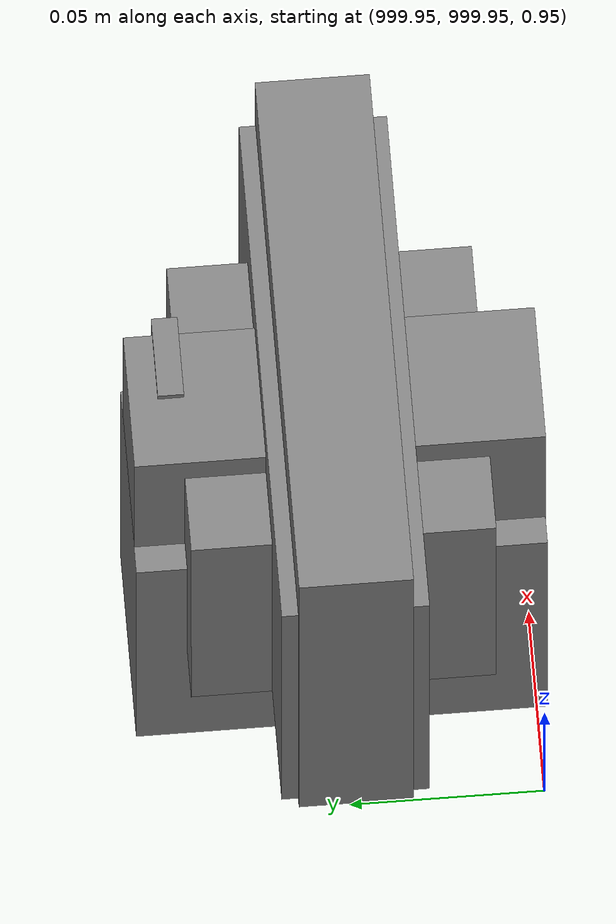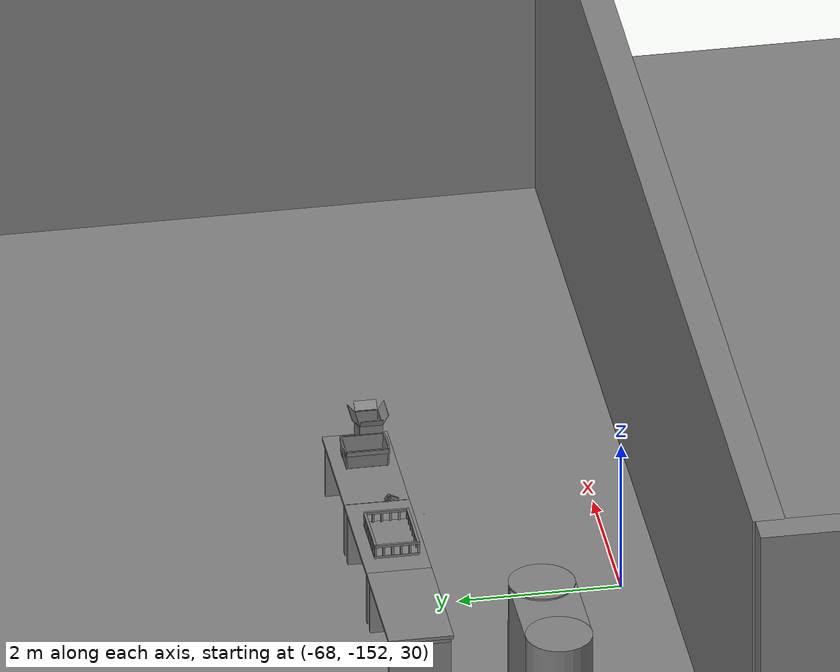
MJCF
<mujoco>
    <option gravity="0.000000000 0.000000000 -9.810000420" timestep="0.0049999999" integrator="implicitfast" density="1.225" viscosity="1.8000001e-05" noslip_iterations="10" iterations="100" sdf_iterations="50">
        <flag multiccd="disable"/>
    </option>
    <size memory="1000M"/>
    <compiler coordinate="local"/>
    <worldbody>
        <light cutoff="30" pos="0 1 1" dir="0 -1 -2"/>
        <light cutoff="30" pos="0 -1 1" dir="0 1 -2"/>
        <body pos="1000.000000000 1000.000000000 1.000000000" euler="0.000000000 0.000000000 180.000000000" name="openloong_gripper_2f85_fix_base_usda_wifi_box">
            <geom contype="1" conaffinity="1" density="1000" type="box" material="" rgba="0.500000000 0.500000000 0.500000000 1.000000000" solimp="0.899999976 0.949999988 0.001000000" friction="1.000000000 0.005000000 0.000100000" solref="0.020000000 1.000000000" margin="0" condim="3" group="0" pos="0.000000000 0.000000000 0.058978677" quat="0.000000000 0.000000047 0.000000000 1.000000000" size="0.068499997 0.018999999 0.059000000" name="openloong_gripper_2f85_fix_base_usda_geom_95BD36D2_B4E3_4926_8FBC_79059EC19110"/>
            <freejoint name="openloong_gripper_2f85_fix_base_usda_wifi_box_joint"/>
            <site size="0.005000000 0.005000000 0.005000000" rgba="0.500000000 0.500000000 0.500000000 1.000000000" pos="0.000000000 0.000000000 0.000000000" quat="0.999961913 0.008726500 0.000000000 0.000000000" group="0" type="sphere" name="openloong_gripper_2f85_fix_base_usda_wifi_boxsite"/>
        </body>
        <body pos="-66.091667175 -149.581192017 31.165288925" euler="158.924682617 -12.433371544 -95.147293091" mocap="true" name="spotlight1_SpotLight"/>
        <body pos="1000.000000000 1000.000000000 1.000000000" euler="0.000011953 0.000005123 -179.999984741" name="openloong_gripper_2f85_fix_base_usda_intel_box">
            <geom contype="1" conaffinity="1" density="1000" type="box" material="" rgba="0.500000000 0.500000000 0.500000000 1.000000000" solimp="0.899999976 0.949999988 0.001000000" friction="1.000000000 0.005000000 0.000100000" solref="0.020000000 1.000000000" margin="0" condim="3" group="0" pos="0.000000000 -0.000067139 0.000082284" quat="0.707106709 0.000000225 0.000000253 0.707106650" size="0.052800003 0.025300000 0.052800003" name="openloong_gripper_2f85_fix_base_usda_geom_76583A48_5101_4BAB_9FFE_795ABF7766DB"/>
            <freejoint name="openloong_gripper_2f85_fix_base_usda_intel_box_joint"/>
            <site size="0.005000000 0.005000000 0.005000000" rgba="0.500000000 0.500000000 0.500000000 1.000000000" pos="0.000000000 0.000000000 0.000000000" quat="0.999961913 0.008726500 0.000000000 0.000000000" group="0" type="sphere" name="openloong_gripper_2f85_fix_base_usda_intel_boxsite"/>
        </body>
        <body pos="-65.987304688 -148.869567871 31.166366577" euler="68.267623901 -60.799568176 -63.815116882" mocap="true" name="spotlight5_SpotLight"/>
        <body pos="1000.000000000 999.999938965 1.000000000" euler="0.000000000 0.000000000 180.000000000" name="openloong_gripper_2f85_fix_base_usda_intelcore_i5">
            <geom contype="1" conaffinity="1" density="1000" type="box" material="" rgba="0.500000000 0.500000000 0.500000000 1.000000000" solimp="0.899999976 0.949999988 0.001000000" friction="1.000000000 0.005000000 0.000100000" solref="0.020000000 1.000000000" margin="0" condim="3" group="0" pos="0.000000000 0.000000000 0.051722717" quat="0.707106709 0.000000000 0.000000000 -0.707106769" size="0.052800000 0.018080002 0.052800000" name="openloong_gripper_2f85_fix_base_usda_geom_FB5F9AB2_0E6E_42A8_9879_E1C4C9F615EF"/>
            <freejoint name="openloong_gripper_2f85_fix_base_usda_intelcore_i5_joint"/>
            <site size="0.005000000 0.005000000 0.005000000" rgba="0.500000000 0.500000000 0.500000000 1.000000000" pos="0.000000000 0.000000000 0.000000000" quat="0.999961913 0.008726534 0.000000000 0.000000000" group="0" type="sphere" name="openloong_gripper_2f85_fix_base_usda_intelcore_i5site"/>
        </body>
        <body pos="1000.000000000 1000.000000000 1.000000000" euler="0.000000000 0.000000000 180.000000000" name="openloong_gripper_2f85_fix_base_usda_cpu_fan">
            <geom contype="1" conaffinity="1" density="1000" type="box" material="" rgba="0.500000000 0.500000000 0.500000000 1.000000000" solimp="0.899999976 0.949999988 0.001000000" friction="1.000000000 0.005000000 0.000100000" solref="0.020000000 1.000000000" margin="0" condim="3" group="0" pos="0.000000000 0.000000000 0.070034981" quat="0.000000000 0.000000000 0.000000000 1.000000000" size="0.070700005 0.014699999 0.070700005" name="openloong_gripper_2f85_fix_base_usda_geom_C7954C97_0D01_4084_93DE_5C581DE69DCD"/>
            <freejoint name="openloong_gripper_2f85_fix_base_usda_cpu_fan_joint"/>
            <site size="0.005000000 0.005000000 0.005000000" rgba="0.500000000 0.500000000 0.500000000 1.000000000" pos="0.000000000 0.000000000 0.000000000" quat="0.999961913 0.008726535 0.000000000 0.000000000" group="0" type="sphere" name="openloong_gripper_2f85_fix_base_usda_cpu_fancsite"/>
        </body>
        <body pos="-65.799270630 -149.594192505 31.169433594" euler="35.524211884 -76.025398254 112.322181702" mocap="true" name="spotlight3_SpotLight"/>
        <body pos="1000.000000000 1000.000000000 1.000000000" euler="0.000000000 0.000000000 180.000000000" name="openloong_gripper_2f85_fix_base_usda_battery_01">
            <geom contype="1" conaffinity="1" density="1000" type="box" material="" rgba="0.500000000 0.500000000 0.500000000 1.000000000" solimp="0.899999976 0.949999988 0.001000000" friction="1.000000000 0.005000000 0.000100000" solref="0.020000000 1.000000000" margin="0" condim="3" group="0" pos="-0.011123657 -0.041940309 0.101691343" quat="1.000000000 0.000000000 0.000000000 0.000000000" size="0.010800000 0.003375000 0.004725000" name="openloong_gripper_2f85_fix_base_usda_geom_2924658A_01E6_4D5A_A099_985023C2273C"/>
            <geom contype="1" conaffinity="1" density="1000" type="box" material="" rgba="0.500000000 0.500000000 0.500000000 1.000000000" solimp="0.899999976 0.949999988 0.001000000" friction="1.000000000 0.005000000 0.000100000" solref="0.020000000 1.000000000" margin="0" condim="3" group="0" pos="-0.010876465 -0.044247437 0.047066893" quat="0.998702705 -0.050920475 0.000000000 0.000000000" size="0.009450001 0.002700000 0.024975000" name="openloong_gripper_2f85_fix_base_usda_geom_A1542E8E_A870_4410_AE62_0E23633DB10D"/>
            <geom contype="1" conaffinity="1" density="1000" type="box" material="" rgba="0.500000000 0.500000000 0.500000000 1.000000000" solimp="0.899999976 0.949999988 0.001000000" friction="1.000000000 0.005000000 0.000100000" solref="0.020000000 1.000000000" margin="0" condim="3" group="0" pos="-0.001235962 -0.000659180 0.047381196" quat="1.000000000 0.000000000 0.000000000 0.000000000" size="0.039420001 0.039150000 0.047250003" name="openloong_gripper_2f85_fix_base_usda_geom_C7AC336B_2CB0_4CA1_A4BD_580B537C7075"/>
            <geom contype="1" conaffinity="1" density="1000" type="box" material="" rgba="0.500000000 0.500000000 0.500000000 1.000000000" solimp="0.899999976 0.949999988 0.001000000" friction="1.000000000 0.005000000 0.000100000" solref="0.020000000 1.000000000" margin="0" condim="3" group="0" pos="-0.010876465 -0.039138794 0.009851727" quat="1.000000000 0.000000000 0.000000000 0.000000000" size="0.009450001 0.010800000 0.013500000" name="openloong_gripper_2f85_fix_base_usda_geom_A61ECA49_18FC_4495_A6ED_B6A142E74BEB"/>
            <geom contype="1" conaffinity="1" density="1000" type="box" material="" rgba="0.500000000 0.500000000 0.500000000 1.000000000" solimp="0.899999976 0.949999988 0.001000000" friction="1.000000000 0.005000000 0.000100000" solref="0.020000000 1.000000000" margin="0" condim="3" group="0" pos="-0.010876465 -0.041528322 0.071508206" quat="1.000000000 0.000000000 0.000000000 0.000000000" size="0.009450001 0.002700000 0.027000001" name="openloong_gripper_2f85_fix_base_usda_geom_71F3EF4A_FFA4_47A5_8386_958BB1066D83"/>
            <freejoint name="openloong_gripper_2f85_fix_base_usda_battery_01_joint"/>
            <site size="0.005000000 0.005000000 0.005000000" rgba="0.500000000 0.500000000 0.500000000 1.000000000" pos="0.000000000 0.000000000 0.000000000" quat="0.999961913 0.008726500 0.000000000 0.000000000" group="0" type="sphere" name="openloong_gripper_2f85_fix_base_usda_battery_01site"/>
        </body>
        <body pos="-64.866622925 -149.383972168 30.183746338" euler="89.999984741 89.999946594 0.000000000" name="openloong_gripper_2f85_fix_base_usda_bluebox_01">
            <geom contype="1" conaffinity="1" density="1000" type="box" material="" rgba="0.500000000 0.500000000 0.500000000 1.000000000" solimp="0.899999976 0.949999988 0.001000000" friction="1.000000000 0.005000000 0.000100000" solref="0.020000000 1.000000000" margin="0" condim="3" group="0" pos="0.276580811 0.187225342 0.000068665" quat="0.707106948 0.000077471 0.707106352 0.000077486" size="0.100000001 0.057999998 0.010000000" name="openloong_gripper_2f85_fix_base_usda_geom_385C20C3_36BA_4E30_B8C7_F05A0DCBAC94"/>
            <geom contype="1" conaffinity="1" density="1000" type="box" material="" rgba="0.500000000 0.500000000 0.500000000 1.000000000" solimp="0.899999976 0.949999988 0.001000000" friction="1.000000000 0.005000000 0.000100000" solref="0.020000000 1.000000000" margin="0" condim="3" group="0" pos="0.000000000 0.002883911 0.000000000" quat="0.999999881 0.000000000 0.000000000 0.000000000" size="0.254000008 0.003000000 0.172000006" name="openloong_gripper_2f85_fix_base_usda_geom_91EBC4AA_AA31_4DC9_8DA2_3216BD34A35B"/>
            <geom contype="1" conaffinity="1" density="1000" type="box" material="" rgba="0.500000000 0.500000000 0.500000000 1.000000000" solimp="0.899999976 0.949999988 0.001000000" friction="1.000000000 0.005000000 0.000100000" solref="0.020000000 1.000000000" margin="0" condim="3" group="0" pos="0.000000000 0.124874115 0.173484802" quat="0.999796331 0.020176515 -0.000000015 0.000000030" size="0.259999990 0.119999997 0.007000000" name="openloong_gripper_2f85_fix_base_usda_geom_0F9017FC_606C_4593_A9D3_4DA8725F94C7"/>
            <geom contype="1" conaffinity="1" density="1000" type="box" material="" rgba="0.500000000 0.500000000 0.500000000 1.000000000" solimp="0.899999976 0.949999988 0.001000000" friction="1.000000000 0.005000000 0.000100000" solref="0.020000000 1.000000000" margin="0" condim="3" group="0" pos="0.000000000 0.124874115 -0.173469543" quat="0.999796331 -0.020176545 -0.000000015 0.000000000" size="0.259999990 0.119999997 0.007000000" name="openloong_gripper_2f85_fix_base_usda_geom_155EF400_F7FD_4E89_8C20_0185C318F5AC"/>
            <geom contype="1" conaffinity="1" density="1000" type="box" material="" rgba="0.500000000 0.500000000 0.500000000 1.000000000" solimp="0.899999976 0.949999988 0.001000000" friction="1.000000000 0.005000000 0.000100000" solref="0.020000000 1.000000000" margin="0" condim="3" group="0" pos="0.000000000 0.214008331 0.188980103" quat="0.999912977 0.013176724 0.000000015 0.000000000" size="0.259999990 0.029999999 0.012500000" name="openloong_gripper_2f85_fix_base_usda_geom_E39A2C97_E0D3_451B_A621_7D63AAD2A8AA"/>
            <geom contype="1" conaffinity="1" density="1000" type="box" material="" rgba="0.500000000 0.500000000 0.500000000 1.000000000" solimp="0.899999976 0.949999988 0.001000000" friction="1.000000000 0.005000000 0.000100000" solref="0.020000000 1.000000000" margin="0" condim="3" group="0" pos="-0.258361816 0.125289917 0.001876831" quat="0.702796936 -0.020792112 0.710783124 0.020769298" size="0.189999998 0.119999997 0.009000000" name="openloong_gripper_2f85_fix_base_usda_geom_4D0BC2A1_AA05_4790_98B5_55B6A6299E9F"/>
            <geom contype="1" conaffinity="1" density="1000" type="box" material="" rgba="0.500000000 0.500000000 0.500000000 1.000000000" solimp="0.899999976 0.949999988 0.001000000" friction="1.000000000 0.005000000 0.000100000" solref="0.020000000 1.000000000" margin="0" condim="3" group="0" pos="0.000000000 0.214008331 -0.188980103" quat="0.999912977 -0.013176769 0.000000030 0.000000015" size="0.259999990 0.029999999 0.012500000" name="openloong_gripper_2f85_fix_base_usda_geom_3EBEF22F_3410_4231_9A21_9DBB834BFEC7"/>
            <geom contype="1" conaffinity="1" density="1000" type="box" material="" rgba="0.500000000 0.500000000 0.500000000 1.000000000" solimp="0.899999976 0.949999988 0.001000000" friction="1.000000000 0.005000000 0.000100000" solref="0.020000000 1.000000000" margin="0" condim="3" group="0" pos="-0.276611328 0.187225342 0.000068665" quat="0.707106650 0.000077441 0.707106709 0.000077456" size="0.100000001 0.057999998 0.010000000" name="openloong_gripper_2f85_fix_base_usda_geom_34B37543_3C2C_49D5_A817_5A76CB4840FB"/>
            <geom contype="1" conaffinity="1" density="1000" type="box" material="" rgba="0.500000000 0.500000000 0.500000000 1.000000000" solimp="0.899999976 0.949999988 0.001000000" friction="1.000000000 0.005000000 0.000100000" solref="0.020000000 1.000000000" margin="0" condim="3" group="0" pos="0.258331299 0.125289917 0.001876831" quat="0.702851415 0.018856421 0.710823774 -0.019329369" size="0.189999998 0.119999997 0.009000000" name="openloong_gripper_2f85_fix_base_usda_geom_596B5EC7_D43A_4FAB_808D_017FB88FA15E"/>
            <freejoint name="openloong_gripper_2f85_fix_base_usda_bluebox_01_joint"/>
            <site size="0.005000000 0.005000000 0.005000000" rgba="0.500000000 0.500000000 0.500000000 1.000000000" pos="0.000000000 0.000000000 0.000000000" quat="0.999961913 0.008726534 0.000000000 0.000000000" group="0" type="sphere" name="openloong_gripper_2f85_fix_base_usda_bluebox_01site"/>
        </body>
        <body pos="-64.496299744 -149.491867065 30.235729218" euler="0.000000000 0.000000000 89.999946594" name="openloong_gripper_2f85_fix_base_usda_cardboardbox_01">
            <geom contype="1" conaffinity="1" density="1000" type="box" material="" rgba="0.500000000 0.500000000 0.500000000 1.000000000" solimp="0.899999976 0.949999988 0.001000000" friction="1.000000000 0.005000000 0.000100000" solref="0.020000000 1.000000000" margin="0" condim="3" group="0" pos="-0.003166199 -0.004086494 0.005052090" quat="1.000000000 0.000000000 0.000000000 0.000000000" size="0.142499998 0.177500010 0.005000000" name="openloong_gripper_2f85_fix_base_usda_geom_65C8551A_C041_42D7_B443_F88DF2A252AC"/>
            <geom contype="1" conaffinity="1" density="1000" type="box" material="" rgba="0.500000000 0.500000000 0.500000000 1.000000000" solimp="0.899999976 0.949999988 0.001000000" friction="1.000000000 0.005000000 0.000100000" solref="0.020000000 1.000000000" margin="0" condim="3" group="0" pos="-0.003166199 0.170316696 0.150570869" quat="1.000000000 0.000000000 0.000000000 0.000000000" size="0.142499998 0.005000000 0.149999991" name="openloong_gripper_2f85_fix_base_usda_geom_26191C8A_9E89_4433_84A5_3F90515EB878"/>
            <geom contype="1" conaffinity="1" density="1000" type="box" material="" rgba="0.500000000 0.500000000 0.500000000 1.000000000" solimp="0.899999976 0.949999988 0.001000000" friction="1.000000000 0.005000000 0.000100000" solref="0.020000000 1.000000000" margin="0" condim="3" group="0" pos="-0.147399902 -0.005307198 0.150570869" quat="1.000000000 0.000000000 0.000000000 0.000000000" size="0.005000000 0.177500010 0.149999991" name="openloong_gripper_2f85_fix_base_usda_geom_97602BE5_60C5_4EEA_9FB5_BEA11B5EF18E"/>
            <geom contype="1" conaffinity="1" density="1000" type="box" material="" rgba="0.500000000 0.500000000 0.500000000 1.000000000" solimp="0.899999976 0.949999988 0.001000000" friction="1.000000000 0.005000000 0.000100000" solref="0.020000000 1.000000000" margin="0" condim="3" group="0" pos="0.140275955 -0.005307198 0.150570869" quat="1.000000000 0.000000000 0.000000000 0.000000000" size="0.005000000 0.177500010 0.149999991" name="openloong_gripper_2f85_fix_base_usda_geom_C5F05BCF_A9F0_4730_962B_1A0E8C4B1C10"/>
            <geom contype="1" conaffinity="1" density="1000" type="box" material="" rgba="0.500000000 0.500000000 0.500000000 1.000000000" solimp="0.899999976 0.949999988 0.001000000" friction="1.000000000 0.005000000 0.000100000" solref="0.020000000 1.000000000" margin="0" condim="3" group="0" pos="-0.003166199 -0.181550980 0.150570869" quat="1.000000000 0.000000000 0.000000000 0.000000000" size="0.142499998 0.005000000 0.149999991" name="openloong_gripper_2f85_fix_base_usda_geom_D2DAC2FB_4740_4C9F_9B40_3C8B80CB1AFA"/>
            <freejoint name="openloong_gripper_2f85_fix_base_usda_cardboardbox_01_joint"/>
            <site size="0.005000000 0.005000000 0.005000000" rgba="0.500000000 0.500000000 0.500000000 1.000000000" pos="0.000000000 0.000000000 0.000000000" quat="0.999961913 0.008726535 0.000000000 0.000000000" group="0" type="sphere" name="openloong_gripper_2f85_fix_base_usda_site_CC325EAF_2951_43F2_8646_7F35B48947E4"/>
            <body pos="0.139160156 -0.004048347 0.301930904" euler="-179.999954224 49.383502960 179.999954224" name="openloong_gripper_2f85_fix_base_usda_A1_006">
                <geom contype="1" conaffinity="1" density="1000" type="box" material="" rgba="0.500000000 0.500000000 0.500000000 1.000000000" solimp="0.899999976 0.949999988 0.001000000" friction="1.000000000 0.005000000 0.000100000" solref="0.020000000 1.000000000" margin="0" condim="3" group="0" pos="-0.071587563 0.000009537 0.001745224" quat="0.999999881 0.000000000 0.000000000 0.000000000" size="0.071249999 0.179999992 0.002500000" name="openloong_gripper_2f85_fix_base_usda_geom_7FE92AE3_DE03_4FBE_81B0_B78FC5948AEE"/>
                <joint armature="0" stiffness="0.07" damping="0.0099999998" axis="0.000000 1.000000 0.000000" type="hinge" name="openloong_gripper_2f85_fix_base_usda_A1_006"/>
            </body>
            <body pos="-0.145902634 -0.004086494 0.301938057" euler="-180.000000000 -60.000011444 -180.000000000" name="openloong_gripper_2f85_fix_base_usda_A2_006">
                <geom contype="1" conaffinity="1" density="1000" type="box" material="" rgba="0.500000000 0.500000000 0.500000000 1.000000000" solimp="0.899999976 0.949999988 0.001000000" friction="1.000000000 0.005000000 0.000100000" solref="0.020000000 1.000000000" margin="0" condim="3" group="0" pos="0.071268082 0.000009537 0.002717972" quat="0.000002921 0.000000000 -0.000000030 0.999999881" size="0.071249999 0.179999992 0.002500000" name="openloong_gripper_2f85_fix_base_usda_geom_0F9EF464_6180_4AA1_B1F7_638C5F7FB073"/>
                <joint armature="0" stiffness="0.07" damping="0.0099999998" axis="0.000000 1.000000 0.000000" type="hinge" name="openloong_gripper_2f85_fix_base_usda_A2_006"/>
            </body>
            <body pos="-0.003385544 0.175991058 0.301930904" euler="-125.858116150 -0.000004561 0.000002331" name="openloong_gripper_2f85_fix_base_usda_B2_006">
                <geom contype="1" conaffinity="1" density="1000" type="box" material="" rgba="0.500000000 0.500000000 0.500000000 1.000000000" solimp="0.899999976 0.949999988 0.001000000" friction="1.000000000 0.005000000 0.000100000" solref="0.020000000 1.000000000" margin="0" condim="3" group="0" pos="0.000009537 -0.070939064 -0.002470016" quat="0.999614120 0.027776197 -0.000000015 0.000000030" size="0.137500003 0.064999998 0.005000000" name="openloong_gripper_2f85_fix_base_usda_geom_10503168_4D31_431E_A2EE_21CF362FBB12"/>
                <joint armature="0" stiffness="0.07" damping="0.0099999998" axis="1.000000 0.000000 0.000000" type="hinge" name="openloong_gripper_2f85_fix_base_usda_B2_006"/>
            </body>
            <body pos="-0.003385544 -0.184140205 0.301938057" euler="147.805557251 0.000000000 0.000000000" name="openloong_gripper_2f85_fix_base_usda_B1_006">
                <geom contype="1" conaffinity="1" density="1000" type="box" material="" rgba="0.500000000 0.500000000 0.500000000 1.000000000" solimp="0.899999976 0.949999988 0.001000000" friction="1.000000000 0.005000000 0.000100000" solref="0.020000000 1.000000000" margin="0" condim="3" group="0" pos="-0.000028610 0.070202351 -0.002703667" quat="0.999614179 -0.027776167 0.000000000 0.000000000" size="0.137500003 0.064999998 0.005000000" name="openloong_gripper_2f85_fix_base_usda_geom_1767DC9B_3EDA_4EF3_A338_B2C3592237F6"/>
                <joint armature="0" stiffness="0.07" damping="0.0099999998" axis="1.000000 0.000000 0.000000" type="hinge" name="openloong_gripper_2f85_fix_base_usda_B1_006"/>
            </body>
        </body>
        <body pos="-65.882858276 -149.481979370 30.229999542" euler="-64.487716675 0.000000000 0.000000000" name="openloong_gripper_2f85_fix_base_usda_Barcode">
            <geom contype="1" conaffinity="1" density="1000" type="box" material="" rgba="0.500000000 0.500000000 0.500000000 1.000000000" solimp="0.899999976 0.949999988 0.001000000" friction="1.000000000 0.005000000 0.000100000" solref="0.020000000 1.000000000" margin="0" condim="3" group="0" pos="0.000000000 0.013038635 0.001419067" quat="0.000000000 0.000000000 0.000000000 1.000000119" size="0.034000002 0.010000000 0.017999999" name="openloong_gripper_2f85_fix_base_usda_geom_63786185_C294_47BE_8EFB_95011D6DCD10"/>
            <geom contype="1" conaffinity="1" density="1000" type="box" material="" rgba="0.500000000 0.500000000 0.500000000 1.000000000" solimp="0.899999976 0.949999988 0.001000000" friction="1.000000000 0.005000000 0.000100000" solref="0.020000000 1.000000000" margin="0" condim="3" group="0" pos="0.000000000 -0.035301208 -0.007095337" quat="0.000000000 0.000000000 -0.043619365 0.999048233" size="0.028999999 0.010000000 0.020000000" name="openloong_gripper_2f85_fix_base_usda_geom_11D81953_0628_467B_8890_B7BCD2820C6F"/>
            <geom contype="1" conaffinity="1" density="1000" type="box" material="" rgba="0.500000000 0.500000000 0.500000000 1.000000000" solimp="0.899999976 0.949999988 0.001000000" friction="1.000000000 0.005000000 0.000100000" solref="0.020000000 1.000000000" margin="0" condim="3" group="0" pos="0.000000000 -0.043411255 -0.011749268" quat="0.922262907 0.386563420 0.000000000 0.000000000" size="0.026000001 0.010000000 0.020000000" name="openloong_gripper_2f85_fix_base_usda_geom_E0774777_5C14_439E_99FF_1D5CE3258E0B"/>
            <geom contype="1" conaffinity="1" density="1000" type="box" material="" rgba="0.500000000 0.500000000 0.500000000 1.000000000" solimp="0.899999976 0.949999988 0.001000000" friction="1.000000000 0.005000000 0.000100000" solref="0.020000000 1.000000000" margin="0" condim="3" group="0" pos="0.000000000 -0.016967773 -0.031860352" quat="0.000000000 0.000000000 0.000000000 1.000000119" size="0.008000000 0.010000000 0.013000000" name="openloong_gripper_2f85_fix_base_usda_geom_FDDFFA18_B5DA_4AB6_BA5E_659D70CB70DE"/>
            <geom contype="1" conaffinity="1" density="1000" type="box" material="" rgba="0.500000000 0.500000000 0.500000000 1.000000000" solimp="0.899999976 0.949999988 0.001000000" friction="1.000000000 0.005000000 0.000100000" solref="0.020000000 1.000000000" margin="0" condim="3" group="0" pos="0.000000000 -0.001869202 0.000312805" quat="0.953716993 0.300705761 0.000000000 0.000000000" size="0.032000002 0.010000000 0.018999999" name="openloong_gripper_2f85_fix_base_usda_geom_3F7E2A6D_FBE3_4CEF_BC3B_0A669CB337F3"/>
            <geom contype="1" conaffinity="1" density="1000" type="box" material="" rgba="0.500000000 0.500000000 0.500000000 1.000000000" solimp="0.899999976 0.949999988 0.001000000" friction="1.000000000 0.005000000 0.000100000" solref="0.020000000 1.000000000" margin="0" condim="3" group="0" pos="0.000000000 -0.019531250 -0.003173828" quat="0.953716993 0.300705761 0.000000000 0.000000000" size="0.030999999 0.010000000 0.020000000" name="openloong_gripper_2f85_fix_base_usda_geom_78812C3F_60E5_4396_BF95_BB5216E97ADE"/>
            <geom contype="1" conaffinity="1" density="1000" type="box" material="" rgba="0.500000000 0.500000000 0.500000000 1.000000000" solimp="0.899999976 0.949999988 0.001000000" friction="1.000000000 0.005000000 0.000100000" solref="0.020000000 1.000000000" margin="0" condim="3" group="0" pos="0.000000000 -0.035301208 -0.007095337" quat="0.953716993 0.300705761 0.000000000 0.000000000" size="0.028999999 0.010000000 0.020000000" name="openloong_gripper_2f85_fix_base_usda_geom_5A3B9793_2BD7_40B2_926A_4441C4B49F81"/>
            <geom contype="1" conaffinity="1" density="1000" type="box" material="" rgba="0.500000000 0.500000000 0.500000000 1.000000000" solimp="0.899999976 0.949999988 0.001000000" friction="1.000000000 0.005000000 0.000100000" solref="0.020000000 1.000000000" margin="0" condim="3" group="0" pos="0.000000000 -0.042617798 -0.071121216" quat="0.000000000 0.000000000 0.000000000 1.000000119" size="0.013000000 0.021000000 0.059999999" name="openloong_gripper_2f85_fix_base_usda_geom_127AEA0E_7160_46F7_9CE9_67B83C92C104"/>
            <freejoint name="openloong_gripper_2f85_fix_base_usda_Barcode_joint"/>
            <site size="0.005000000 0.005000000 0.005000000" rgba="0.500000000 0.500000000 0.500000000 1.000000000" pos="0.000000000 0.000000000 0.000000000" quat="1.000000000 0.000000000 0.000000000 0.000000000" group="0" type="sphere" name="openloong_gripper_2f85_fix_base_usda_Barcode_site"/>
        </body>
        <body pos="-66.745018005 -149.392349243 30.184000015" euler="0.000000000 0.000000000 89.999946594" name="[22331660149502]_Basket_01">
            <geom contype="1" conaffinity="1" density="1000" type="box" material="" rgba="0.500000000 0.500000000 0.500000000 1.000000000" solimp="0.899999976 0.949999988 0.001000000" friction="1.000000000 0.005000000 0.000100000" solref="0.020000000 1.000000000" margin="0" condim="3" group="0" pos="-0.052425385 0.389207840 0.089787483" quat="0.707107008 0.000000000 0.000000000 0.707106411" size="0.014249999 0.014249999 0.059999999" name="[22331660149502]_geom_6502C2A1_799C_4242_9D2C_70B487AB63B0"/>
            <geom contype="1" conaffinity="1" density="1000" type="box" material="" rgba="0.500000000 0.500000000 0.500000000 1.000000000" solimp="0.899999976 0.949999988 0.001000000" friction="1.000000000 0.005000000 0.000100000" solref="0.020000000 1.000000000" margin="0" condim="3" group="0" pos="0.264015198 -0.133043289 0.089787483" quat="0.707107008 0.000000000 0.000000000 0.707106411" size="0.014249999 0.014249999 0.059999999" name="[22331660149502]_geom_EADA183E_75C6_45B8_B6B3_B419A1F54306"/>
            <geom contype="1" conaffinity="1" density="1000" type="box" material="" rgba="0.500000000 0.500000000 0.500000000 1.000000000" solimp="0.899999976 0.949999988 0.001000000" friction="1.000000000 0.005000000 0.000100000" solref="0.020000000 1.000000000" margin="0" condim="3" group="0" pos="-0.264015198 -0.265548706 0.089793205" quat="0.707107008 0.000000000 0.000000000 0.707106411" size="0.014249999 0.014249999 0.059999999" name="[22331660149502]_geom_6E879A3E_5788_405A_953D_30641FDEBC3B"/>
            <geom contype="1" conaffinity="1" density="1000" type="box" material="" rgba="0.500000000 0.500000000 0.500000000 1.000000000" solimp="0.899999976 0.949999988 0.001000000" friction="1.000000000 0.005000000 0.000100000" solref="0.020000000 1.000000000" margin="0" condim="3" group="0" pos="-0.160263062 -0.389322281 0.089793205" quat="0.707107008 0.000000000 0.000000000 0.707106411" size="0.014249999 0.014249999 0.059999999" name="[22331660149502]_geom_4FAF2E77_E34A_4E1F_AD78_D1B1371C543B"/>
            <geom contype="1" conaffinity="1" density="1000" type="box" material="" rgba="0.500000000 0.500000000 0.500000000 1.000000000" solimp="0.899999976 0.949999988 0.001000000" friction="1.000000000 0.005000000 0.000100000" solref="0.020000000 1.000000000" margin="0" condim="3" group="0" pos="0.162265778 -0.389322281 0.089787483" quat="0.707107008 0.000000000 0.000000000 0.707106411" size="0.014249999 0.014249999 0.059999999" name="[22331660149502]_geom_9492C96B_D8CD_4F96_87C0_65323103A14C"/>
            <geom contype="1" conaffinity="1" density="1000" type="box" material="" rgba="0.500000000 0.500000000 0.500000000 1.000000000" solimp="0.899999976 0.949999988 0.001000000" friction="1.000000000 0.005000000 0.000100000" solref="0.020000000 1.000000000" margin="0" condim="3" group="0" pos="0.264015198 0.389207840 0.089787483" quat="0.707107008 0.000000000 0.000000000 0.707106411" size="0.014249999 0.014249999 0.059999999" name="[22331660149502]_geom_56E9DB37_D9C5_43F8_89DF_97AFC70A151E"/>
            <geom contype="1" conaffinity="1" density="1000" type="box" material="" rgba="0.500000000 0.500000000 0.500000000 1.000000000" solimp="0.899999976 0.949999988 0.001000000" friction="1.000000000 0.005000000 0.000100000" solref="0.020000000 1.000000000" margin="0" condim="3" group="0" pos="-0.264015198 -0.133043289 0.089793205" quat="0.707107008 0.000000000 0.000000000 0.707106411" size="0.014249999 0.014249999 0.059999999" name="[22331660149502]_geom_70D1B5D5_5B4C_4511_AD9C_848E4F1DA34E"/>
            <geom contype="1" conaffinity="1" density="1000" type="box" material="" rgba="0.500000000 0.500000000 0.500000000 1.000000000" solimp="0.899999976 0.949999988 0.001000000" friction="1.000000000 0.005000000 0.000100000" solref="0.020000000 1.000000000" margin="0" condim="3" group="0" pos="-0.264026642 0.269256592 0.089793205" quat="0.707107008 0.000000000 0.000000000 0.707106411" size="0.014249999 0.014249999 0.059999999" name="[22331660149502]_geom_8F5330DE_A3B6_47B6_BF59_153E2C53DAE9"/>
            <geom contype="1" conaffinity="1" density="1000" type="box" material="" rgba="0.500000000 0.500000000 0.500000000 1.000000000" solimp="0.899999976 0.949999988 0.001000000" friction="1.000000000 0.005000000 0.000100000" solref="0.020000000 1.000000000" margin="0" condim="3" group="0" pos="0.054462433 0.389207840 0.089787483" quat="0.707107008 0.000000000 0.000000000 0.707106411" size="0.014249999 0.014249999 0.059999999" name="[22331660149502]_geom_501CC5DA_A2A5_465E_A76C_43C62485EDD5"/>
            <geom contype="1" conaffinity="1" density="1000" type="box" material="" rgba="0.500000000 0.500000000 0.500000000 1.000000000" solimp="0.899999976 0.949999988 0.001000000" friction="1.000000000 0.005000000 0.000100000" solref="0.020000000 1.000000000" margin="0" condim="3" group="0" pos="0.054462433 -0.389322281 0.089787483" quat="0.707107008 0.000000000 0.000000000 0.707106411" size="0.014249999 0.014249999 0.059999999" name="[22331660149502]_geom_115299FC_5D45_4B14_ACE4_38FAC4257DA6"/>
            <geom contype="1" conaffinity="1" density="1000" type="box" material="" rgba="0.500000000 0.500000000 0.500000000 1.000000000" solimp="0.899999976 0.949999988 0.001000000" friction="1.000000000 0.005000000 0.000100000" solref="0.020000000 1.000000000" margin="0" condim="3" group="0" pos="0.264015198 0.269256592 0.089793205" quat="0.707107008 0.000000000 0.000000000 0.707106411" size="0.014249999 0.014249999 0.059999999" name="[22331660149502]_geom_C969E2BE_AE54_4818_86D8_992D246E8DD2"/>
            <geom contype="1" conaffinity="1" density="1000" type="box" material="" rgba="0.500000000 0.500000000 0.500000000 1.000000000" solimp="0.899999976 0.949999988 0.001000000" friction="1.000000000 0.005000000 0.000100000" solref="0.020000000 1.000000000" margin="0" condim="3" group="0" pos="0.264015198 -0.389322281 0.089787483" quat="0.707107008 0.000000000 0.000000000 0.707106411" size="0.014249999 0.014249999 0.059999999" name="[22331660149502]_geom_32D3DD96_AEE8_4B11_8DC3_C90056D547F9"/>
            <geom contype="1" conaffinity="1" density="1000" type="box" material="" rgba="0.500000000 0.500000000 0.500000000 1.000000000" solimp="0.899999976 0.949999988 0.001000000" friction="1.000000000 0.005000000 0.000100000" solref="0.020000000 1.000000000" margin="0" condim="3" group="0" pos="0.000000000 0.000000000 0.015998840" quat="0.707107008 0.000000000 0.000000000 0.707106411" size="0.403499991 0.279000014 0.015750000" name="[22331660149502]_geom_F51B19EF_036D_4013_AA70_292462A71859"/>
            <geom contype="1" conaffinity="1" density="1000" type="box" material="" rgba="0.500000000 0.500000000 0.500000000 1.000000000" solimp="0.899999976 0.949999988 0.001000000" friction="1.000000000 0.005000000 0.000100000" solref="0.020000000 1.000000000" margin="0" condim="3" group="0" pos="0.000000000 -0.389476776 0.163619041" quat="0.707107008 0.000000000 0.000000000 0.707106411" size="0.015000000 0.277500004 0.015750000" name="[22331660149502]_geom_14A75681_7305_4379_B349_8F0D15815342"/>
            <geom contype="1" conaffinity="1" density="1000" type="box" material="" rgba="0.500000000 0.500000000 0.500000000 1.000000000" solimp="0.899999976 0.949999988 0.001000000" friction="1.000000000 0.005000000 0.000100000" solref="0.020000000 1.000000000" margin="0" condim="3" group="0" pos="0.162265778 0.389207840 0.089787483" quat="0.707107008 0.000000000 0.000000000 0.707106411" size="0.014249999 0.014249999 0.059999999" name="[22331660149502]_geom_555B7288_61F6_461F_A073_0DEF55A65756"/>
            <geom contype="1" conaffinity="1" density="1000" type="box" material="" rgba="0.500000000 0.500000000 0.500000000 1.000000000" solimp="0.899999976 0.949999988 0.001000000" friction="1.000000000 0.005000000 0.000100000" solref="0.020000000 1.000000000" margin="0" condim="3" group="0" pos="0.000000000 0.389471054 0.163619041" quat="0.707107008 0.000000000 0.000000000 0.707106411" size="0.015000000 0.277500004 0.015750000" name="[22331660149502]_geom_84CADE18_72E6_40E6_9580_31551E348CFB"/>
            <geom contype="1" conaffinity="1" density="1000" type="box" material="" rgba="0.500000000 0.500000000 0.500000000 1.000000000" solimp="0.899999976 0.949999988 0.001000000" friction="1.000000000 0.005000000 0.000100000" solref="0.020000000 1.000000000" margin="0" condim="3" group="0" pos="-0.263511658 0.000000000 0.163619041" quat="0.707107008 0.000000000 0.000000000 0.707106411" size="0.403499991 0.015000000 0.015750000" name="[22331660149502]_geom_47DB2215_C239_4B23_93AE_BAA999EF1F7F"/>
            <geom contype="1" conaffinity="1" density="1000" type="box" material="" rgba="0.500000000 0.500000000 0.500000000 1.000000000" solimp="0.899999976 0.949999988 0.001000000" friction="1.000000000 0.005000000 0.000100000" solref="0.020000000 1.000000000" margin="0" condim="3" group="0" pos="-0.264015198 0.141334534 0.089793205" quat="0.707107008 0.000000000 0.000000000 0.707106411" size="0.014249999 0.014249999 0.059999999" name="[22331660149502]_geom_C74C24DF_6251_4C53_9974_BBD8905B3C28"/>
            <geom contype="1" conaffinity="1" density="1000" type="box" material="" rgba="0.500000000 0.500000000 0.500000000 1.000000000" solimp="0.899999976 0.949999988 0.001000000" friction="1.000000000 0.005000000 0.000100000" solref="0.020000000 1.000000000" margin="0" condim="3" group="0" pos="0.264015198 -0.265548706 0.089787483" quat="0.707107008 0.000000000 0.000000000 0.707106411" size="0.014249999 0.014249999 0.059999999" name="[22331660149502]_geom_F7AFBAF1_8D20_41C5_BE18_787A15CF9180"/>
            <geom contype="1" conaffinity="1" density="1000" type="box" material="" rgba="0.500000000 0.500000000 0.500000000 1.000000000" solimp="0.899999976 0.949999988 0.001000000" friction="1.000000000 0.005000000 0.000100000" solref="0.020000000 1.000000000" margin="0" condim="3" group="0" pos="-0.160263062 0.389207840 0.089787483" quat="0.707107008 0.000000000 0.000000000 0.707106411" size="0.014249999 0.014249999 0.059999999" name="[22331660149502]_geom_6DD46CA3_BF25_4F8B_A28F_7B4C6879BA55"/>
            <geom contype="1" conaffinity="1" density="1000" type="box" material="" rgba="0.500000000 0.500000000 0.500000000 1.000000000" solimp="0.899999976 0.949999988 0.001000000" friction="1.000000000 0.005000000 0.000100000" solref="0.020000000 1.000000000" margin="0" condim="3" group="0" pos="-0.052425385 -0.389322281 0.089787483" quat="0.707107008 0.000000000 0.000000000 0.707106411" size="0.014249999 0.014249999 0.059999999" name="[22331660149502]_geom_B6442FE6_6A82_46BD_B97F_32F28DF7F894"/>
            <geom contype="1" conaffinity="1" density="1000" type="box" material="" rgba="0.500000000 0.500000000 0.500000000 1.000000000" solimp="0.899999976 0.949999988 0.001000000" friction="1.000000000 0.005000000 0.000100000" solref="0.020000000 1.000000000" margin="0" condim="3" group="0" pos="-0.264026642 -0.389322281 0.089793205" quat="0.707107008 0.000000000 0.000000000 0.707106411" size="0.014249999 0.014249999 0.059999999" name="[22331660149502]_geom_1D821404_F9B0_4C63_A002_3B3252543C28"/>
            <geom contype="1" conaffinity="1" density="1000" type="box" material="" rgba="0.500000000 0.500000000 0.500000000 1.000000000" solimp="0.899999976 0.949999988 0.001000000" friction="1.000000000 0.005000000 0.000100000" solref="0.020000000 1.000000000" margin="0" condim="3" group="0" pos="0.264015198 0.141334534 0.089787483" quat="0.707107008 0.000000000 0.000000000 0.707106411" size="0.014249999 0.014249999 0.059999999" name="[22331660149502]_geom_6DD89B53_F92E_41BC_9AF0_66DFA898B5EE"/>
            <geom contype="1" conaffinity="1" density="1000" type="box" material="" rgba="0.500000000 0.500000000 0.500000000 1.000000000" solimp="0.899999976 0.949999988 0.001000000" friction="1.000000000 0.005000000 0.000100000" solref="0.020000000 1.000000000" margin="0" condim="3" group="0" pos="-0.264015198 0.389207840 0.089793205" quat="0.707107008 0.000000000 0.000000000 0.707106411" size="0.014249999 0.014249999 0.059999999" name="[22331660149502]_geom_FF458397_F646_48DC_8F00_A35B128EE8A9"/>
            <geom contype="1" conaffinity="1" density="1000" type="box" material="" rgba="0.500000000 0.500000000 0.500000000 1.000000000" solimp="0.899999976 0.949999988 0.001000000" friction="1.000000000 0.005000000 0.000100000" solref="0.020000000 1.000000000" margin="0" condim="3" group="0" pos="0.264015198 0.004480362 0.089787483" quat="0.707107008 0.000000000 0.000000000 0.707106411" size="0.014249999 0.014249999 0.059999999" name="[22331660149502]_geom_CCA99F56_B721_4EA9_A5C9_229433894FC3"/>
            <geom contype="1" conaffinity="1" density="1000" type="box" material="" rgba="0.500000000 0.500000000 0.500000000 1.000000000" solimp="0.899999976 0.949999988 0.001000000" friction="1.000000000 0.005000000 0.000100000" solref="0.020000000 1.000000000" margin="0" condim="3" group="0" pos="0.263694763 -0.000011444 0.163619041" quat="0.707107008 0.000000000 0.000000000 0.707106411" size="0.403499991 0.015000000 0.015750000" name="[22331660149502]_geom_658EBB8E_2A80_4FBD_AB65_17285B093113"/>
            <geom contype="1" conaffinity="1" density="1000" type="box" material="" rgba="0.500000000 0.500000000 0.500000000 1.000000000" solimp="0.899999976 0.949999988 0.001000000" friction="1.000000000 0.005000000 0.000100000" solref="0.020000000 1.000000000" margin="0" condim="3" group="0" pos="-0.264015198 0.004480362 0.089793205" quat="0.707107008 0.000000000 0.000000000 0.707106411" size="0.014249999 0.014249999 0.059999999" name="[22331660149502]_geom_473B796A_5C2F_4037_AECF_0DCD6D8EC7DF"/>
            <freejoint name="[22331660149502]_joint_41AB5274_816A_473D_82CE_9B4B540F5E93"/>
        </body>
        <body pos="0.000000000 0.000000000 0.000000000" euler="0.000000000 0.000000000 0.000000000" name="Static Objects_Static Objects">
            <geom contype="1" conaffinity="1" density="1000" type="box" material="" rgba="0.500000000 0.500000000 0.500000000 1.000000000" solimp="0.899999976 0.949999988 0.001000000" friction="1.000000000 0.005000000 0.000100000" solref="0.020000000 1.000000000" margin="0" condim="3" group="0" pos="-67.544113159 -149.365814209 29.727830887" quat="0.500000417 0.499999970 0.499999553 0.499999970" size="0.381000012 0.319999993 0.041000001" name="Static Objects_geom_2200A3C7_7BD4_4980_9D22_2A06F011684A"/>
            <geom contype="1" conaffinity="1" density="1000" type="box" material="" rgba="0.500000000 0.500000000 0.500000000 1.000000000" solimp="0.899999976 0.949999988 0.001000000" friction="1.000000000 0.005000000 0.000100000" solref="0.020000000 1.000000000" margin="0" condim="3" group="0" pos="-68.239501953 -149.365814209 30.086868286" quat="0.500000417 0.499999970 0.499999553 0.499999970" size="0.370999992 0.039500002 0.745000005" name="Static Objects_geom_C7B4533A_FBAF_4483_99CD_4717D7B46EF5"/>
            <geom contype="1" conaffinity="1" density="1000" type="box" material="" rgba="0.500000000 0.500000000 0.500000000 1.000000000" solimp="0.899999976 0.949999988 0.001000000" friction="1.000000000 0.005000000 0.000100000" solref="0.020000000 1.000000000" margin="0" condim="3" group="0" pos="-68.239501953 -149.365814209 30.147235870" quat="0.500000417 0.499999970 0.499999553 0.499999970" size="0.400000006 0.022000000 0.800000012" name="Static Objects_geom_76C2D2E6_B10E_4378_9451_0CFD9D8A427B"/>
            <geom contype="1" conaffinity="1" density="1000" type="box" material="" rgba="0.500000000 0.500000000 0.500000000 1.000000000" solimp="0.899999976 0.949999988 0.001000000" friction="1.000000000 0.005000000 0.000100000" solref="0.020000000 1.000000000" margin="0" condim="3" group="0" pos="-68.934890747 -149.365814209 29.727830887" quat="0.500000417 0.499999970 0.499999553 0.499999970" size="0.381000012 0.319999993 0.041000001" name="Static Objects_geom_F1AC2010_677F_4E0F_A27D_5BB750D661BA"/>
            <geom contype="1" conaffinity="1" density="1000" type="box" material="" rgba="0.500000000 0.500000000 0.500000000 1.000000000" solimp="0.899999976 0.949999988 0.001000000" friction="1.000000000 0.005000000 0.000100000" solref="0.020000000 1.000000000" margin="0" condim="3" group="0" pos="-68.239501953 -149.365814209 29.561563492" quat="0.500000417 0.499999970 0.499999553 0.499999970" size="0.020000000 0.022000000 0.660000026" name="Static Objects_geom_B40AF547_D87C_47CB_BE35_DEC895903DA9"/>
            <geom contype="1" conaffinity="1" density="1000" type="box" material="" rgba="0.500000000 0.500000000 0.500000000 1.000000000" solimp="0.899999976 0.949999988 0.001000000" friction="1.000000000 0.005000000 0.000100000" solref="0.020000000 1.000000000" margin="0" condim="3" group="0" pos="-65.945671082 -149.365814209 29.727830887" quat="0.500000417 0.499999970 0.499999553 0.499999970" size="0.381000012 0.319999993 0.041000001" name="Static Objects_geom_F9C2395D_EF06_4C56_962A_1C8FE44C64D2"/>
            <geom contype="1" conaffinity="1" density="1000" type="box" material="" rgba="0.500000000 0.500000000 0.500000000 1.000000000" solimp="0.899999976 0.949999988 0.001000000" friction="1.000000000 0.005000000 0.000100000" solref="0.020000000 1.000000000" margin="0" condim="3" group="0" pos="-66.641059875 -149.365814209 30.086868286" quat="0.500000417 0.499999970 0.499999553 0.499999970" size="0.370999992 0.039500002 0.745000005" name="Static Objects_geom_8E488080_FA1B_4E57_92D5_6C678D7A2673"/>
            <geom contype="1" conaffinity="1" density="1000" type="box" material="" rgba="0.500000000 0.500000000 0.500000000 1.000000000" solimp="0.899999976 0.949999988 0.001000000" friction="1.000000000 0.005000000 0.000100000" solref="0.020000000 1.000000000" margin="0" condim="3" group="0" pos="-66.641059875 -149.365814209 30.147235870" quat="0.500000417 0.499999970 0.499999553 0.499999970" size="0.400000006 0.022000000 0.800000012" name="Static Objects_geom_1D523AE2_F5CC_4472_91AB_659C0558B42F"/>
            <geom contype="1" conaffinity="1" density="1000" type="box" material="" rgba="0.500000000 0.500000000 0.500000000 1.000000000" solimp="0.899999976 0.949999988 0.001000000" friction="1.000000000 0.005000000 0.000100000" solref="0.020000000 1.000000000" margin="0" condim="3" group="0" pos="-67.336448669 -149.365814209 29.727830887" quat="0.500000417 0.499999970 0.499999553 0.499999970" size="0.381000012 0.319999993 0.041000001" name="Static Objects_geom_0BA50348_C7A1_46B7_BFC4_640DEB648CB5"/>
            <geom contype="1" conaffinity="1" density="1000" type="box" material="" rgba="0.500000000 0.500000000 0.500000000 1.000000000" solimp="0.899999976 0.949999988 0.001000000" friction="1.000000000 0.005000000 0.000100000" solref="0.020000000 1.000000000" margin="0" condim="3" group="0" pos="-66.641059875 -149.365814209 29.561563492" quat="0.500000417 0.499999970 0.499999553 0.499999970" size="0.020000000 0.022000000 0.660000026" name="Static Objects_geom_41421953_70D5_49EA_89F6_6905400B88E0"/>
            <geom contype="1" conaffinity="1" density="1000" type="box" material="" rgba="0.500000000 0.500000000 0.500000000 1.000000000" solimp="0.899999976 0.949999988 0.001000000" friction="1.000000000 0.005000000 0.000100000" solref="0.020000000 1.000000000" margin="0" condim="3" group="0" pos="-64.338577271 -149.365814209 29.727830887" quat="0.500000417 0.499999970 0.499999553 0.499999970" size="0.381000012 0.319999993 0.041000001" name="Static Objects_geom_54A68EF0_026B_4F23_84F0_0D3D938AA715"/>
            <geom contype="1" conaffinity="1" density="1000" type="box" material="" rgba="0.500000000 0.500000000 0.500000000 1.000000000" solimp="0.899999976 0.949999988 0.001000000" friction="1.000000000 0.005000000 0.000100000" solref="0.020000000 1.000000000" margin="0" condim="3" group="0" pos="-65.033966064 -149.365814209 30.086868286" quat="0.500000417 0.499999970 0.499999553 0.499999970" size="0.370999992 0.039500002 0.745000005" name="Static Objects_geom_036F01B3_3CAD_4997_B89A_826002916F6A"/>
            <geom contype="1" conaffinity="1" density="1000" type="box" material="" rgba="0.500000000 0.500000000 0.500000000 1.000000000" solimp="0.899999976 0.949999988 0.001000000" friction="1.000000000 0.005000000 0.000100000" solref="0.020000000 1.000000000" margin="0" condim="3" group="0" pos="-65.033966064 -149.365814209 30.147235870" quat="0.500000417 0.499999970 0.499999553 0.499999970" size="0.400000006 0.022000000 0.800000012" name="Static Objects_geom_CCA12CEB_FDE1_4E4A_B32B_9CBAF4D7B600"/>
            <geom contype="1" conaffinity="1" density="1000" type="box" material="" rgba="0.500000000 0.500000000 0.500000000 1.000000000" solimp="0.899999976 0.949999988 0.001000000" friction="1.000000000 0.005000000 0.000100000" solref="0.020000000 1.000000000" margin="0" condim="3" group="0" pos="-65.729354858 -149.365814209 29.727830887" quat="0.500000417 0.499999970 0.499999553 0.499999970" size="0.381000012 0.319999993 0.041000001" name="Static Objects_geom_13922F0D_66DB_4837_A8D9_70D3E8D44452"/>
            <geom contype="1" conaffinity="1" density="1000" type="box" material="" rgba="0.500000000 0.500000000 0.500000000 1.000000000" solimp="0.899999976 0.949999988 0.001000000" friction="1.000000000 0.005000000 0.000100000" solref="0.020000000 1.000000000" margin="0" condim="3" group="0" pos="-65.033966064 -149.365814209 29.561563492" quat="0.500000417 0.499999970 0.499999553 0.499999970" size="0.020000000 0.022000000 0.660000026" name="Static Objects_geom_19723AF0_D118_4C47_9CC8_3091BC6DB672"/>
            <geom contype="1" conaffinity="1" density="1000" type="box" material="" rgba="0.500000000 0.500000000 0.500000000 1.000000000" solimp="0.899999976 0.949999988 0.001000000" friction="1.000000000 0.005000000 0.000100000" solref="0.020000000 1.000000000" margin="0" condim="3" group="0" pos="-61.754566193 -137.853729248 33.906845093" quat="0.707107067 0.000000000 0.000000000 0.707106471" size="0.759999990 0.759999990 4.500000000" name="Static Objects_geom_868D580E_9992_461E_A58A_829CA16A206F"/>
            <geom contype="1" conaffinity="1" density="1000" type="box" material="" rgba="0.500000000 0.500000000 0.500000000 1.000000000" solimp="0.899999976 0.949999988 0.001000000" friction="1.000000000 0.005000000 0.000100000" solref="0.020000000 1.000000000" margin="0" condim="3" group="0" pos="-57.511135101 -144.927108765 31.707921982" quat="1.000000000 0.000000000 0.000000000 0.000000000" size="0.200000003 8.000000000 2.299999952" name="Static Objects_geom_E01BBDC8_9201_4260_A611_A573C701687A"/>
            <geom contype="1" conaffinity="1" density="1000" type="box" material="" rgba="0.500000000 0.500000000 0.500000000 1.000000000" solimp="0.899999976 0.949999988 0.001000000" friction="1.000000000 0.005000000 0.000100000" solref="0.020000000 1.000000000" margin="0" condim="3" group="0" pos="-80.517646790 -157.574050903 31.688196182" quat="0.707107067 0.000000000 0.000000000 0.707106471" size="0.600000024 0.600000024 2.299999952" name="Static Objects_geom_3370E094_4849_4532_9893_5AFE9C99C505"/>
            <geom contype="1" conaffinity="1" density="1000" type="box" material="" rgba="0.500000000 0.500000000 0.500000000 1.000000000" solimp="0.899999976 0.949999988 0.001000000" friction="1.000000000 0.005000000 0.000100000" solref="0.020000000 1.000000000" margin="0" condim="3" group="0" pos="-80.711044312 -147.414932251 31.666158676" quat="1.000000000 0.000000000 0.000000000 0.000000000" size="0.200000003 10.000000000 2.299999952" name="Static Objects_geom_935AB28A_7669_456E_B635_535824680AC3"/>
            <geom contype="1" conaffinity="1" density="1000" type="box" material="" rgba="0.500000000 0.500000000 0.500000000 1.000000000" solimp="0.899999976 0.949999988 0.001000000" friction="1.000000000 0.005000000 0.000100000" solref="0.020000000 1.000000000" margin="0" condim="3" group="0" pos="-57.687217712 -137.434692383 31.688196182" quat="0.707107067 0.000000000 0.000000000 0.707106471" size="0.600000024 0.600000024 2.299999952" name="Static Objects_geom_1384A4A8_547A_4923_B107_4AB3821B825C"/>
            <geom contype="1" conaffinity="1" density="1000" type="box" material="" rgba="0.500000000 0.500000000 0.500000000 1.000000000" solimp="0.899999976 0.949999988 0.001000000" friction="1.000000000 0.005000000 0.000100000" solref="0.020000000 1.000000000" margin="0" condim="3" group="0" pos="-69.537033081 -140.263229370 31.714921951" quat="0.707107067 0.000000000 0.000000000 0.707106471" size="0.759999990 4.500000000 2.299999952" name="Static Objects_geom_24E87B9E_42DD_4BBB_AE8F_841674A38A2E"/>
            <geom contype="1" conaffinity="1" density="1000" type="box" material="" rgba="0.500000000 0.500000000 0.500000000 1.000000000" solimp="0.899999976 0.949999988 0.001000000" friction="1.000000000 0.005000000 0.000100000" solref="0.020000000 1.000000000" margin="0" condim="3" group="0" pos="-80.073638916 -137.853713989 33.906845093" quat="0.707107067 0.000000000 0.000000000 0.707106471" size="0.759999990 0.759999990 4.500000000" name="Static Objects_geom_80C06BBD_44EA_443B_917B_43455D186419"/>
            <geom contype="1" conaffinity="1" density="1000" type="box" material="" rgba="0.500000000 0.500000000 0.500000000 1.000000000" solimp="0.899999976 0.949999988 0.001000000" friction="1.000000000 0.005000000 0.000100000" solref="0.020000000 1.000000000" margin="0" condim="3" group="0" pos="-73.406707764 -155.734664917 31.707921982" quat="1.000000000 0.000000000 0.000000000 0.000000000" size="0.200000003 3.000000000 2.299999952" name="Static Objects_geom_836C46DC_507D_426A_96DC_4C10DD516DEC"/>
            <geom contype="1" conaffinity="1" density="1000" type="box" material="" rgba="0.500000000 0.500000000 0.500000000 1.000000000" solimp="0.899999976 0.949999988 0.001000000" friction="1.000000000 0.005000000 0.000100000" solref="0.020000000 1.000000000" margin="0" condim="3" group="0" pos="-68.497543335 -137.448257446 31.707921982" quat="0.707107067 0.000000000 0.000000000 0.707106471" size="0.200000003 14.000000000 2.299999952" name="Static Objects_geom_B1D99065_D201_4499_A648_3F584377B3E8"/>
            <geom contype="1" conaffinity="1" density="1000" type="cylinder" material="" rgba="0.500000000 0.500000000 0.500000000 1.000000000" solimp="0.899999976 0.949999988 0.001000000" friction="1.000000000 0.005000000 0.000100000" solref="0.020000000 1.000000000" margin="0" condim="3" group="0" pos="-68.868522644 -142.134506226 31.711090088" quat="0.707107067 0.000000000 0.000000000 0.707106471" size="0.509999990 2.299999952 1.000000000" name="Static Objects_geom_2E5577B1_401E_4093_A213_5BCBDC3BB914"/>
            <geom contype="1" conaffinity="1" density="1000" type="plane" material="" rgba="0.500000000 0.500000000 0.500000000 1.000000000" solimp="0.899999976 0.949999988 0.001000000" friction="1.000000000 0.005000000 0.000100000" solref="0.020000000 1.000000000" margin="0" condim="3" group="0" pos="-72.873703003 -147.131927490 29.409669876" quat="1.000000000 0.000000000 0.000000000 0.000000000" size="18.000000000 14.000000000 1.000000000" name="Static Objects_geom_98C0B813_1697_48E0_BE10_0CCE8B6248C2"/>
            <geom contype="1" conaffinity="1" density="1000" type="box" material="" rgba="0.500000000 0.500000000 0.500000000 1.000000000" solimp="0.899999976 0.949999988 0.001000000" friction="1.000000000 0.005000000 0.000100000" solref="0.020000000 1.000000000" margin="0" condim="3" group="0" pos="-79.943580627 -157.782272339 31.707921982" quat="0.707107067 0.000000000 0.000000000 0.707106471" size="0.200000003 7.000000000 2.299999952" name="Static Objects_geom_13F4CBB6_473A_4994_AF0F_80321BD6A06A"/>
            <geom contype="1" conaffinity="1" density="1000" type="box" material="" rgba="0.500000000 0.500000000 0.500000000 1.000000000" solimp="0.899999976 0.949999988 0.001000000" friction="1.000000000 0.005000000 0.000100000" solref="0.020000000 1.000000000" margin="0" condim="3" group="0" pos="-65.421028137 -152.903442383 31.707921982" quat="0.707107067 0.000000000 0.000000000 0.707106471" size="0.200000003 7.800000191 2.299999952" name="Static Objects_geom_9379D510_F185_40E7_B562_D32638C5AFE1"/>
            <geom contype="1" conaffinity="1" density="1000" type="box" material="" rgba="0.500000000 0.500000000 0.500000000 1.000000000" solimp="0.899999976 0.949999988 0.001000000" friction="1.000000000 0.005000000 0.000100000" solref="0.020000000 1.000000000" margin="0" condim="3" group="0" pos="-74.776908875 -149.964416504 31.688196182" quat="1.000000000 0.000000000 0.000000000 0.000000000" size="0.600000024 0.409999996 2.299999952" name="Static Objects_geom_6AD555EB_18CA_46E7_B1D6_02E1C3C9729C"/>
            <geom contype="1" conaffinity="1" density="1000" type="cylinder" material="" rgba="0.500000000 0.500000000 0.500000000 1.000000000" solimp="0.899999976 0.949999988 0.001000000" friction="1.000000000 0.005000000 0.000100000" solref="0.020000000 1.000000000" margin="0" condim="3" group="0" pos="-60.161884308 -142.134506226 31.711090088" quat="0.707107067 0.000000000 0.000000000 0.707106471" size="0.509999990 2.299999952 1.000000000" name="Static Objects_geom_EA27863D_6AC6_442A_A642_A9A8CA024797"/>
            <geom contype="1" conaffinity="1" density="1000" type="cylinder" material="" rgba="0.500000000 0.500000000 0.500000000 1.000000000" solimp="0.899999976 0.949999988 0.001000000" friction="1.000000000 0.005000000 0.000100000" solref="0.020000000 1.000000000" margin="0" condim="3" group="0" pos="-75.382453918 -149.963455200 31.711090088" quat="0.707107067 0.000000000 0.000000000 0.707106471" size="0.409999996 2.299999952 1.000000000" name="Static Objects_geom_B6CFD589_3C1E_4DBA_B7A9_CA8872B627D0"/>
            <geom contype="1" conaffinity="1" density="1000" type="cylinder" material="" rgba="0.500000000 0.500000000 0.500000000 1.000000000" solimp="0.899999976 0.949999988 0.001000000" friction="1.000000000 0.005000000 0.000100000" solref="0.020000000 1.000000000" margin="0" condim="3" group="0" pos="-74.154960632 -149.963455200 31.711090088" quat="0.707107067 0.000000000 0.000000000 0.707106471" size="0.409999996 2.299999952 1.000000000" name="Static Objects_geom_CF7807D6_384F_4C63_AB4B_190FB36867E0"/>
            <geom contype="1" conaffinity="1" density="1000" type="cylinder" material="" rgba="0.500000000 0.500000000 0.500000000 1.000000000" solimp="0.899999976 0.949999988 0.001000000" friction="1.000000000 0.005000000 0.000100000" solref="0.020000000 1.000000000" margin="0" condim="3" group="0" pos="-77.566612244 -142.134506226 31.711090088" quat="0.707107067 0.000000000 0.000000000 0.707106471" size="0.509999990 2.299999952 1.000000000" name="Static Objects_geom_D066D521_D310_412F_BAAD_A90C8D862E44"/>
        </body>
        <body pos="-66.291030884 -149.869689941 29.018842697" euler="0.000000000 0.000000000 89.999946594" mocap="true" name="openloong_gripper_2f85_fix_base_usda_leftHandMocap"/>
        <body pos="-66.291030884 -149.869689941 29.018842697" euler="0.000000000 0.000000000 89.999946594" mocap="true" name="openloong_gripper_2f85_fix_base_usda_rightHandMocap"/>
        <body pos="-66.291030884 -149.869689941 30.218843460" euler="0.000000000 0.000000000 89.999946594" name="openloong_gripper_2f85_fix_base_usda_base_link">
            <geom contype="1" conaffinity="1" density="1000" type="mesh" material="" rgba="0.783999979 0.783999979 0.783999979 1.000000000" solimp="0.899999976 0.949999988 0.001000000" friction="1.000000000 0.005000000 0.000100000" solref="0.020000000 1.000000000" margin="0" condim="3" group="3" mesh="base_link" pos="0.000000000 0.000000000 0.000000000" quat="1.000000000 0.000000000 0.000000000 0.000000000" size="1.000000000 1.000000000 1.000000000" name="openloong_gripper_2f85_fix_base_usda__geom_7_7115A0A9_686D_469A_A2F3_BE1687563538"/>
            <site size="0.005000000 0.005000000 0.005000000" rgba="0.500000000 0.500000000 0.500000000 1.000000000" pos="0.000000000 0.000000000 0.000000000" quat="1.000000000 0.000000000 0.000000000 0.000000000" group="0" type="sphere" name="openloong_gripper_2f85_fix_base_usda_imu"/>
            <inertial mass="22.447001" pos="-0.005664100 -0.001336700 0.238289997" diaginertia="0.374352545 0.277180195 0.220617250" quat="0.999247074 0.035235517 -0.015086859 0.006023135"/>
            <body pos="0.000000000 0.000000000 0.299997330" euler="0.000000000 0.000000000 0.000000000" name="openloong_gripper_2f85_fix_base_usda_dummy_body">
                <geom contype="1" conaffinity="1" density="1000" type="sphere" material="" rgba="0.783999979 0.783999979 0.783999979 1.000000000" solimp="0.899999976 0.949999988 0.001000000" friction="1.000000000 0.005000000 0.000100000" solref="0.020000000 1.000000000" margin="0" condim="3" group="3" pos="0.000000000 0.000000000 0.000000000" quat="1.000000000 0.000000000 0.000000000 0.000000000" size="0.010000000 0.000000000 0.000000000" name="openloong_gripper_2f85_fix_base_usda__geom_8_51CA26A8_F324_4453_8421_95498FD633BA"/>
                <joint armature="0.0099999998" stiffness="0" damping="0.1" axis="0.000000 0.000000 1.000000" type="hinge" name="openloong_gripper_2f85_fix_base_usda_dummy_joint"/>
                <site size="0.010000000 0.005000000 0.005000000" rgba="0.500000000 0.500000000 0.500000000 1.000000000" pos="0.000000000 0.000000000 0.000000000" quat="1.000000000 0.000000000 0.000000000 0.000000000" group="3" type="sphere" name="openloong_gripper_2f85_fix_base_usda_dummy_site"/>
            </body>
            <body pos="0.009002686 0.000000000 0.406400681" euler="0.000000000 0.000000000 0.000000000" name="openloong_gripper_2f85_fix_base_usda_Link_head_yaw">
                <geom contype="1" conaffinity="1" density="1000" type="mesh" material="" rgba="0.783999979 0.783999979 0.783999979 1.000000000" solimp="0.899999976 0.949999988 0.001000000" friction="1.000000000 0.005000000 0.000100000" solref="0.020000000 1.000000000" margin="0" condim="3" group="3" mesh="Link_head_yaw" pos="0.000000000 0.000000000 0.000000000" quat="1.000000000 0.000000000 0.000000000 0.000000000" size="1.000000000 1.000000000 1.000000000" name="openloong_gripper_2f85_fix_base_usda__geom_10_215F01EF_3D7D_42D8_97FD_E389EAAB7DA9"/>
                <inertial mass="0.84249002" pos="0.000000000 -0.002081400 0.044801001" diaginertia="0.000700588 0.000629000 0.000553812" quat="0.706933022 -0.015675601 0.015677100 0.706933022"/>
                <body pos="0.000000000 -0.034599304 0.048500061" euler="0.000000000 0.000000000 0.000000000" name="openloong_gripper_2f85_fix_base_usda_Link_head_pitch">
                    <geom contype="1" conaffinity="1" density="1000" type="mesh" material="" rgba="0.783999979 0.783999979 0.783999979 1.000000000" solimp="0.899999976 0.949999988 0.001000000" friction="1.000000000 0.005000000 0.000100000" solref="0.020000000 1.000000000" margin="0" condim="3" group="3" mesh="Link_head_pitch" pos="0.000000000 0.000000000 0.000000000" quat="1.000000000 0.000000000 0.000000000 0.000000000" size="1.000000000 1.000000000 1.000000000" name="openloong_gripper_2f85_fix_base_usda__geom_12_AB54FE2C_3866_43C9_8073_0189FDF0DE35"/>
                    <inertial mass="1.3943" pos="0.020569000 0.033004001 0.125000000" diaginertia="0.006381400 0.006289940 0.004481460" quat="0.973390222 0.008406822 0.228157058 0.019624906"/>
                    <body pos="0.000000000 0.029998779 0.000000000" euler="0.000000000 0.000000000 0.000000000" name="openloong_gripper_2f85_fix_base_usda_neck_center_body">
                        <site size="0.010000000 0.005000000 0.005000000" rgba="0.500000000 0.500000000 0.500000000 1.000000000" pos="0.000000000 0.000000000 0.000000000" quat="1.000000000 0.000000000 0.000000000 0.000000000" group="3" type="sphere" name="openloong_gripper_2f85_fix_base_usda_neck_center_site"/>
                        <body pos="0.020004272 0.000000000 0.149999619" euler="-0.000002229 39.998176575 -90.000205994" name="openloong_gripper_2f85_fix_base_usda_camera_head">
                            <site size="0.010000000 0.005000000 0.005000000" rgba="0.500000000 0.500000000 0.500000000 1.000000000" pos="0.000000000 0.000000000 0.000000000" quat="1.000000000 0.000000000 0.000000000 0.000000000" group="3" type="sphere" name="openloong_gripper_2f85_fix_base_usda_camera_head_site"/>
                        </body>
                    </body>
                </body>
            </body>
            <body pos="0.003997803 -0.161598206 0.392200470" euler="0.000000000 0.000000000 0.000000000" name="openloong_gripper_2f85_fix_base_usda_Link_arm_r_01">
                <geom contype="1" conaffinity="1" density="1000" type="mesh" material="" rgba="0.783999979 0.783999979 0.783999979 1.000000000" solimp="0.899999976 0.949999988 0.001000000" friction="1.000000000 0.005000000 0.000100000" solref="0.020000000 1.000000000" margin="0" condim="3" group="3" mesh="Link_arm_r_01" pos="0.000000000 0.000000000 0.000000000" quat="1.000000000 0.000000000 0.000000000 0.000000000" size="1.000000000 1.000000000 1.000000000" name="openloong_gripper_2f85_fix_base_usda__geom_14_B0E6F054_AC18_4767_B9B0_65F2CD8BBAF9"/>
                <joint armature="0.0099999998" stiffness="0" damping="1" axis="0.000000 -1.000000 0.000000" limited="true" range="-170.000015259 170.000015259" type="hinge" name="openloong_gripper_2f85_fix_base_usda_J_arm_r_01"/>
                <inertial mass="0.75641" pos="0.004494600 -0.038293999 -0.000001874" diaginertia="0.000842990 0.000803050 0.000587120" quat="-0.000163502 0.707098067 0.000812463 0.707115054"/>
                <body pos="-0.041992188 -0.041000366 0.000000000" euler="0.000000000 0.000000000 0.000000000" name="openloong_gripper_2f85_fix_base_usda_Link_arm_r_02">
                    <geom contype="1" conaffinity="1" density="1000" type="mesh" material="" rgba="0.783999979 0.783999979 0.783999979 1.000000000" solimp="0.899999976 0.949999988 0.001000000" friction="1.000000000 0.005000000 0.000100000" solref="0.020000000 1.000000000" margin="0" condim="3" group="3" mesh="Link_arm_r_02" pos="0.000000000 0.000000000 0.000000000" quat="1.000000000 0.000000000 0.000000000 0.000000000" size="1.000000000 1.000000000 1.000000000" name="openloong_gripper_2f85_fix_base_usda__geom_16_ED697F78_0064_4DDC_A695_E310E25BB7A6"/>
                    <joint armature="0.0099999998" stiffness="0" damping="1" axis="-1.000000 0.000000 0.000000" limited="true" range="-105.000244141 105.000244141" type="hinge" name="openloong_gripper_2f85_fix_base_usda_J_arm_r_02"/>
                    <inertial mass="0.98500001" pos="0.041999999 -0.067430697 0.000000000" diaginertia="0.002262690 0.001730990 0.001154020" quat="0.500000000 0.500000000 -0.500000000 0.500000000"/>
                    <body pos="0.041992188 -0.122596741 0.000000000" euler="0.000000000 0.000000000 0.000000000" name="openloong_gripper_2f85_fix_base_usda_Link_arm_r_03">
                        <geom contype="1" conaffinity="1" density="1000" type="mesh" material="" rgba="0.783999979 0.783999979 0.783999979 1.000000000" solimp="0.899999976 0.949999988 0.001000000" friction="1.000000000 0.005000000 0.000100000" solref="0.020000000 1.000000000" margin="0" condim="3" group="3" mesh="Link_arm_r_03" pos="0.000000000 0.000000000 0.000000000" quat="1.000000000 0.000000000 0.000000000 0.000000000" size="1.000000000 1.000000000 1.000000000" name="openloong_gripper_2f85_fix_base_usda__geom_18_D0B3EF74_74AE_4A7C_91E4_72E6D7E24350"/>
                        <joint armature="0.0099999998" stiffness="0" damping="1" axis="0.000000 -1.000000 0.000000" limited="true" range="-170.000015259 170.000015259" type="hinge" name="openloong_gripper_2f85_fix_base_usda_J_arm_r_03"/>
                        <inertial mass="0.95899999" pos="-0.001413580 -0.164663002 0.020757901" diaginertia="0.002101340 0.002064590 0.000754802" quat="0.560480952 0.454391927 -0.443732947 0.531497955"/>
                        <body pos="0.035293579 -0.177406311 0.023998260" euler="0.000000000 0.000000000 0.000000000" name="openloong_gripper_2f85_fix_base_usda_Link_arm_r_04">
                            <geom contype="1" conaffinity="1" density="1000" type="mesh" material="" rgba="0.783999979 0.783999979 0.783999979 1.000000000" solimp="0.899999976 0.949999988 0.001000000" friction="1.000000000 0.005000000 0.000100000" solref="0.020000000 1.000000000" margin="0" condim="3" group="3" mesh="Link_arm_r_04" pos="0.000000000 0.000000000 0.000000000" quat="1.000000000 0.000000000 0.000000000 0.000000000" size="1.000000000 1.000000000 1.000000000" name="openloong_gripper_2f85_fix_base_usda__geom_20_0A1FF5CC_A1CF_4BC5_B211_1046DE0F81CA"/>
                            <joint armature="0.0099999998" stiffness="0" damping="1" axis="-1.000000 0.000000 0.000000" limited="true" range="0.000000000 170.000015259" type="hinge" name="openloong_gripper_2f85_fix_base_usda_J_arm_r_04"/>
                            <inertial mass="0.60000002" pos="-0.038727000 -0.060766999 -0.021003000" diaginertia="0.001092610 0.000712422 0.000645102" quat="0.327701002 0.632602990 -0.467366993 0.523443997"/>
                            <body pos="-0.035293579 -0.103492737 -0.023998260" euler="0.000000000 0.000000000 0.000000000" name="openloong_gripper_2f85_fix_base_usda_Link_arm_r_05">
                                <geom contype="1" conaffinity="1" density="1000" type="mesh" material="" rgba="0.783999979 0.783999979 0.783999979 1.000000000" solimp="0.899999976 0.949999988 0.001000000" friction="1.000000000 0.005000000 0.000100000" solref="0.020000000 1.000000000" margin="0" condim="3" group="3" mesh="Link_arm_r_05" pos="0.000000000 0.000000000 0.000000000" quat="1.000000000 0.000000000 0.000000000 0.000000000" size="1.000000000 1.000000000 1.000000000" name="openloong_gripper_2f85_fix_base_usda__geom_22_E0CCC8AE_A655_4EC2_A09F_6C6F891C71EA"/>
                                <joint armature="0.0099999998" stiffness="0" damping="1" axis="0.000000 -1.000000 0.000000" limited="true" range="-170.000015259 170.000015259" type="hinge" name="openloong_gripper_2f85_fix_base_usda_J_arm_r_05"/>
                                <inertial mass="0.68976003" pos="0.000032712 -0.068658002 -0.000111780" diaginertia="0.002522510 0.002411100 0.000448695" quat="0.707660973 0.706543028 -0.002603360 0.002470550"/>
                                <body pos="-0.026489258 -0.196502686 0.000000000" euler="0.000000000 0.000000000 0.000000000" name="openloong_gripper_2f85_fix_base_usda_Link_arm_r_06">
                                    <geom contype="1" conaffinity="1" density="1000" type="mesh" material="" rgba="0.783999979 0.783999979 0.783999979 1.000000000" solimp="0.899999976 0.949999988 0.001000000" friction="1.000000000 0.005000000 0.000100000" solref="0.020000000 1.000000000" margin="0" condim="3" group="3" mesh="Link_arm_r_06" pos="0.000000000 0.000000000 0.000000000" quat="1.000000000 0.000000000 0.000000000 0.000000000" size="1.000000000 1.000000000 1.000000000" name="openloong_gripper_2f85_fix_base_usda__geom_24_56EAAB4D_98E2_4BF3_A915_883120972A60"/>
                                    <joint armature="0.0099999998" stiffness="0" damping="1" axis="1.000000 0.000000 0.000000" limited="true" range="-105.000244141 105.000244141" type="hinge" name="openloong_gripper_2f85_fix_base_usda_J_arm_r_06"/>
                                    <inertial mass="0.28" pos="0.026078001 -0.000000896 0.001663700" diaginertia="0.000156930 0.000145601 0.000104979" quat="0.707080841 0.001851080 0.001883810 0.707127810"/>
                                    <body pos="0.026489258 0.000000000 0.031799316" euler="0.000000000 0.000000000 0.000000000" name="openloong_gripper_2f85_fix_base_usda_Link_arm_r_07">
                                        <geom contype="1" conaffinity="1" density="1000" type="mesh" material="" rgba="0.783999979 0.783999979 0.783999979 1.000000000" solimp="0.899999976 0.949999988 0.001000000" friction="1.000000000 0.005000000 0.000100000" solref="0.020000000 1.000000000" margin="0" condim="3" group="3" mesh="Link_arm_r_07" pos="0.000000000 0.000000000 0.000000000" quat="1.000000000 0.000000000 0.000000000 0.000000000" size="1.000000000 1.000000000 1.000000000" name="openloong_gripper_2f85_fix_base_usda__geom_26_77907A06_792A_47DC_A2FB_D6BA071425B7"/>
                                        <joint armature="0.0099999998" stiffness="0" damping="1" axis="0.000000 0.000000 1.000000" limited="true" range="-60.000133514 60.000133514" type="hinge" name="openloong_gripper_2f85_fix_base_usda_J_arm_r_07"/>
                                        <inertial mass="0.61353999" pos="-0.007859000 -0.158170000 -0.027736001" diaginertia="0.003037610 0.002570910 0.000729379" quat="0.427542925 0.443532884 -0.553093910 0.560867906"/>
                                        <body pos="0.000000000 0.286994934 -0.270000458" euler="150.000350952 -0.000001649 -0.000000442" name="openloong_gripper_2f85_fix_base_usda_camera_wrist_r">
                                            <site size="0.010000000 0.005000000 0.005000000" rgba="0.500000000 0.500000000 0.500000000 1.000000000" pos="0.000000000 0.000000000 0.000000000" quat="1.000000000 0.000000000 0.000000000 0.000000000" group="3" type="sphere" name="openloong_gripper_2f85_fix_base_usda_camera_wrist_r_site"/>
                                        </body>
                                        <body pos="0.000000000 -0.220008850 -0.033002853" euler="0.000000000 0.000000000 179.999969482" name="openloong_gripper_2f85_fix_base_usda_ee_center_body_r">
                                            <site size="0.010000000 0.005000000 0.005000000" rgba="0.500000000 0.500000000 0.500000000 1.000000000" pos="0.000000000 0.000000000 0.000000000" quat="1.000000000 0.000000000 0.000000000 0.000000000" group="3" type="sphere" name="openloong_gripper_2f85_fix_base_usda_ee_center_site_r"/>
                                        </body>
                                        <body pos="0.000000000 -0.066001892 -0.031000137" euler="89.999984741 0.000000000 180.000000000" name="openloong_gripper_2f85_fix_base_usda_zbr_base_link">
                                            <geom contype="1" conaffinity="1" density="1000" type="mesh" material="" rgba="0.783999979 0.783999979 0.783999979 1.000000000" solimp="0.899999976 0.949999988 0.001000000" friction="1.000000000 0.005000000 0.000100000" solref="0.020000000 1.000000000" margin="0" condim="3" group="3" mesh="base" pos="0.000000000 0.000003815 -0.000007629" quat="1.000000000 0.000000000 0.000000000 0.000000000" size="1.000000238 1.000000238 1.000000238" name="openloong_gripper_2f85_fix_base_usda__geom_30_FE98C8E6_0B2A_4E51_9EE5_72FD0605AF15"/>
                                            <inertial mass="0.77744102" pos="0.000000000 -0.000027039 0.035467502" diaginertia="0.000260285 0.000225381 0.000152708" quat="0.999998808 -0.001528488 0.000000000 0.000000000"/>
                                            <body pos="-0.030609138 0.004745484 0.065696731" euler="-89.999984741 -0.000000000 0.000000000" name="openloong_gripper_2f85_fix_base_usda_r_left_driver">
                                                <geom contype="1" conaffinity="1" density="1000" type="mesh" material="" rgba="0.783999979 0.783999979 0.783999979 1.000000000" solimp="0.899999976 0.949999988 0.001000000" friction="1.000000000 0.005000000 0.000100000" solref="0.020000000 1.000000000" margin="0" condim="3" group="3" mesh="driver" pos="0.030609138 0.054901138 -0.004699708" quat="0.707106829 0.707106709 0.000000000 -0.000000000" size="1.000000238 1.000000238 1.000000238" name="openloong_gripper_2f85_fix_base_usda__geom_32_A8E29DF8_F9E6_41DB_8638_557E4A720462"/>
                                                <joint armature="0.0049999999" stiffness="0" damping="0.1" axis="0.000000 0.000000 1.000000" limited="true" range="0.000000000 51.566200256" type="hinge" name="openloong_gripper_2f85_fix_base_usda_r_left_driver_joint"/>
                                                <inertial mass="0.0089956298" pos="0.000000000 0.017754700 0.001073140" diaginertia="0.000001724 0.000001609 0.000000322" quat="0.681301236 0.732003212 0.000000000 0.000000000"/>
                                                <body pos="-0.031402595 0.004524232 -0.010200503" euler="0.000000000 0.000000000 180.000000000" name="openloong_gripper_2f85_fix_base_usda_r_left_coupler">
                                                    <geom contype="1" conaffinity="1" density="1000" type="mesh" material="" rgba="0.783999979 0.783999979 0.783999979 1.000000000" solimp="0.899999976 0.949999988 0.001000000" friction="1.000000000 0.005000000 0.000100000" solref="0.020000000 1.000000000" margin="0" condim="3" group="3" mesh="coupler" pos="-0.062011734 -0.050354015 0.005500795" quat="0.707106829 -0.707106709 0.000000000 -0.000000000" size="1.000000238 1.000000238 1.000000238" name="openloong_gripper_2f85_fix_base_usda__geom_34_0DF7EA96_8D00_4138_A052_2656B234C3C7"/>
                                                    <inertial mass="0.0140974" pos="0.000000000 0.003012090 0.023217499" diaginertia="0.000004162 0.000003522 0.000000888" quat="0.705635548 -0.045590367 0.045590367 0.705635548"/>
                                                </body>
                                            </body>
                                            <body pos="-0.012695315 -0.012001040 0.072212234" euler="-89.999984741 -0.000000000 0.000000000" name="openloong_gripper_2f85_fix_base_usda_r_left_spring_link">
                                                <geom contype="1" conaffinity="1" density="1000" type="mesh" material="" rgba="0.783999979 0.783999979 0.783999979 1.000000000" solimp="0.899999976 0.949999988 0.001000000" friction="1.000000000 0.005000000 0.000100000" solref="0.020000000 1.000000000" margin="0" condim="3" group="3" mesh="spring_link" pos="0.012695315 0.061416641 0.012050631" quat="0.707106829 0.707106709 0.000000000 -0.000000000" size="1.000000238 1.000000238 1.000000238" name="openloong_gripper_2f85_fix_base_usda__geom_36_602049A4_4097_458E_B448_BF9CABBE681B"/>
                                                <joint armature="0.001" stiffness="0.050000001" damping="0.00125" axis="0.000000 0.000000 1.000000" limited="true" range="-17.000000000 51.566200256" type="hinge" name="openloong_gripper_2f85_fix_base_usda_r_left_spring_link_joint"/>
                                                <inertial mass="0.0221642" pos="-0.000000009 0.018162400 0.021265799" diaginertia="0.000008969 0.000006717 0.000002639" quat="0.663403213 -0.244737089 0.244737089 0.663403213"/>
                                                <body pos="-0.038208015 -0.042503368 0.002950669" euler="180.000000000 0.000000000 -0.002185660" name="openloong_gripper_2f85_fix_base_usda_r_left_follower">
                                                    <geom contype="1" conaffinity="1" density="1000" type="mesh" material="" rgba="0.783999979 0.783999979 0.783999979 1.000000000" solimp="0.899999976 0.949999988 0.001000000" friction="1.000000000 0.005000000 0.000100000" solref="0.020000000 1.000000000" margin="0" condim="3" group="3" mesh="tongue" pos="0.050918590 -0.103920005 -0.009099962" quat="0.707106829 -0.707106709 0.000000030 0.000000030" size="1.000000238 1.000000238 1.000000238" name="openloong_gripper_2f85_fix_base_usda__geom_40_19434115_942E_4669_AE30_9036E93A4AFD"/>
                                                    <geom contype="1" conaffinity="1" density="1000" type="mesh" material="" rgba="0.783999979 0.783999979 0.783999979 1.000000000" solimp="0.899999976 0.949999988 0.001000000" friction="1.000000000 0.005000000 0.000100000" solref="0.020000000 1.000000000" margin="0" condim="3" group="3" mesh="follower" pos="0.050918590 -0.103920005 -0.009099962" quat="0.707106829 -0.707106709 0.000000030 0.000000030" size="1.000000238 1.000000238 1.000000238" name="openloong_gripper_2f85_fix_base_usda__geom_39_7B16981D_292A_4CA5_93C8_DA12C37E1604"/>
                                                    <joint armature="0.001" stiffness="0" damping="0.1" axis="0.000000 0.000000 1.000000" limited="true" range="-49.999961853 51.566200256" type="hinge" name="openloong_gripper_2f85_fix_base_usda_r_left_follower"/>
                                                    <inertial mass="0.0125222" pos="0.000000000 -0.011046000 0.012478600" diaginertia="0.000002674 0.000002456 0.000000602" quat="0.986436546 0.164143041 0.000000000 0.000000000"/>
                                                    <body pos="-0.037765510 -0.103912376 -0.009099962" euler="-89.999984741 0.000000000 0.000004829" name="openloong_gripper_2f85_fix_base_usda_r_left_pad">
                                                        <geom contype="1" conaffinity="1" density="1000" type="box" material="" rgba="0.550000012 0.550000012 0.550000012 1.000000000" solimp="0.949999988 0.990000010 0.001000000" friction="0.699999988 0.005000000 0.000100000" solref="0.020000000 1.000000000" margin="0" condim="3" group="3" mass="1e-06" pos="0.043243419 0.000003815 0.119995147" quat="0.999999881 0.000000000 0.000000000 0.000000000" size="0.002000001 0.011000003 0.009375002" name="openloong_gripper_2f85_fix_base_usda_r_left_pad1_9CBF7C96_AD59_4388_AE11_4815DAE9DAFB"/>
                                                        <geom contype="1" conaffinity="1" density="1000" type="box" material="" rgba="0.449999988 0.449999988 0.449999988 1.000000000" solimp="0.949999988 0.990000010 0.001000000" friction="0.600000024 0.005000000 0.000100000" solref="0.020000000 1.000000000" margin="0" condim="3" group="3" mass="1e-06" pos="0.043243419 0.000003815 0.138748199" quat="0.999999881 0.000000000 0.000000000 0.000000000" size="0.002000001 0.011000003 0.009375002" name="openloong_gripper_2f85_fix_base_usda_r_left_pad2_CD469309_486A_464F_AF87_28CC5CDA049F"/>
                                                    </body>
                                                </body>
                                            </body>
                                            <body pos="0.030593880 -0.004753114 0.065696731" euler="89.999984741 0.000000000 180.000000000" name="openloong_gripper_2f85_fix_base_usda_r_right_driver">
                                                <geom contype="1" conaffinity="1" density="1000" type="mesh" material="" rgba="0.783999979 0.783999979 0.783999979 1.000000000" solimp="0.899999976 0.949999988 0.001000000" friction="1.000000000 0.005000000 0.000100000" solref="0.020000000 1.000000000" margin="0" condim="3" group="3" mesh="driver" pos="0.030593880 0.054901138 -0.004699708" quat="0.707106829 0.707106709 0.000000000 0.000000000" size="1.000000238 1.000000238 1.000000238" name="openloong_gripper_2f85_fix_base_usda__geom_42_84E28421_6440_4093_A5E2_B5DE10F40D3C"/>
                                                <joint armature="0.0049999999" stiffness="0" damping="0.1" axis="0.000000 0.000000 1.000000" limited="true" range="0.000000000 51.566200256" type="hinge" name="openloong_gripper_2f85_fix_base_usda_r_right_driver_joint"/>
                                                <inertial mass="0.0089956298" pos="0.000000000 0.017754700 0.001073140" diaginertia="0.000001724 0.000001609 0.000000322" quat="0.681301236 0.732003212 0.000000000 0.000000000"/>
                                                <body pos="-0.031417854 0.004531861 -0.010202411" euler="0.000000000 0.000000000 180.000000000" name="openloong_gripper_2f85_fix_base_usda_r_right_coupler">
                                                    <geom contype="1" conaffinity="1" density="1000" type="mesh" material="" rgba="0.783999979 0.783999979 0.783999979 1.000000000" solimp="0.899999976 0.949999988 0.001000000" friction="1.000000000 0.005000000 0.000100000" solref="0.020000000 1.000000000" margin="0" condim="3" group="3" mesh="coupler" pos="-0.062042251 -0.050376903 0.005500795" quat="0.707106829 -0.707106709 0.000000000 0.000000000" size="1.000000238 1.000000238 1.000000238" name="openloong_gripper_2f85_fix_base_usda__geom_44_BAF78E9B_63BB_4351_87B8_2E86E753731D"/>
                                                    <inertial mass="0.0140974" pos="0.000000000 0.003012090 0.023217499" diaginertia="0.000004162 0.000003522 0.000000888" quat="0.705635548 -0.045590367 0.045590367 0.705635548"/>
                                                </body>
                                            </body>
                                            <body pos="0.012695315 0.011997226 0.072219864" euler="89.999984741 0.000000000 180.000000000" name="openloong_gripper_2f85_fix_base_usda_r_right_spring_link">
                                                <geom contype="1" conaffinity="1" density="1000" type="mesh" material="" rgba="0.783999979 0.783999979 0.783999979 1.000000000" solimp="0.899999976 0.949999988 0.001000000" friction="1.000000000 0.005000000 0.000100000" solref="0.020000000 1.000000000" margin="0" condim="3" group="3" mesh="spring_link" pos="0.012695315 0.061424270 0.012048724" quat="0.707106829 0.707106709 0.000000000 0.000000000" size="1.000000238 1.000000238 1.000000238" name="openloong_gripper_2f85_fix_base_usda__geom_46_BB2F6270_D0D7_49B2_ABD3_AC97E37B0637"/>
                                                <joint armature="0.001" stiffness="0.050000001" damping="0.00125" axis="0.000000 0.000000 1.000000" limited="true" range="-17.000000000 51.566200256" type="hinge" name="openloong_gripper_2f85_fix_base_usda_r_right_spring_link_joint"/>
                                                <inertial mass="0.0221642" pos="-0.000000009 0.018162400 0.021265799" diaginertia="0.000008969 0.000006717 0.000002639" quat="0.663403213 -0.244737089 0.244737089 0.663403213"/>
                                                <body pos="-0.038208015 -0.042495739 0.002950669" euler="180.000000000 0.000000000 0.000000000" name="openloong_gripper_2f85_fix_base_usda_r_right_follower">
                                                    <geom contype="1" conaffinity="1" density="1000" type="mesh" material="" rgba="0.783999979 0.783999979 0.783999979 1.000000000" solimp="0.899999976 0.949999988 0.001000000" friction="1.000000000 0.005000000 0.000100000" solref="0.020000000 1.000000000" margin="0" condim="3" group="3" mesh="follower" pos="0.050888073 -0.103927635 -0.009099962" quat="0.707106829 -0.707106709 0.000000000 0.000000000" size="1.000000238 1.000000238 1.000000238" name="openloong_gripper_2f85_fix_base_usda__geom_50_7D9F5863_B823_461A_A02D_AA748681E1C8"/>
                                                    <geom contype="1" conaffinity="1" density="1000" type="mesh" material="" rgba="0.783999979 0.783999979 0.783999979 1.000000000" solimp="0.899999976 0.949999988 0.001000000" friction="1.000000000 0.005000000 0.000100000" solref="0.020000000 1.000000000" margin="0" condim="3" group="3" mesh="tongue" pos="0.050888073 -0.103927635 -0.009099962" quat="0.707106829 -0.707106709 0.000000000 0.000000000" size="1.000000238 1.000000238 1.000000238" name="openloong_gripper_2f85_fix_base_usda__geom_49_8E4C0679_1F44_4997_8D2B_F7F8C77D9F56"/>
                                                    <joint armature="0.001" stiffness="0" damping="0.1" axis="0.000000 0.000000 1.000000" limited="true" range="-49.999961853 51.566200256" type="hinge" name="openloong_gripper_2f85_fix_base_usda_r_right_follower_joint"/>
                                                    <inertial mass="0.0125222" pos="0.000000000 -0.011046000 0.012478600" diaginertia="0.000002674 0.000002456 0.000000602" quat="0.986436546 0.164143041 0.000000000 0.000000000"/>
                                                    <body pos="-0.037811287 -0.103927635 -0.009099962" euler="-89.999984741 0.000000000 0.000000000" name="openloong_gripper_2f85_fix_base_usda_r_right_pad">
                                                        <geom contype="1" conaffinity="1" density="1000" type="box" material="" rgba="0.449999988 0.449999988 0.449999988 1.000000000" solimp="0.949999988 0.990000010 0.001000000" friction="0.600000024 0.005000000 0.000100000" solref="0.020000000 1.000000000" margin="0" condim="3" group="3" mass="1e-06" pos="0.043258678 0.000000000 0.138748199" quat="1.000000000 0.000000000 0.000000000 0.000000000" size="0.002000001 0.011000003 0.009375002" name="openloong_gripper_2f85_fix_base_usda_r_right_pad2_4867F1AB_C630_4B67_82B1_F81C65C11FB8"/>
                                                        <geom contype="1" conaffinity="1" density="1000" type="box" material="" rgba="0.550000012 0.550000012 0.550000012 1.000000000" solimp="0.949999988 0.990000010 0.001000000" friction="0.699999988 0.005000000 0.000100000" solref="0.020000000 1.000000000" margin="0" condim="3" group="3" mass="1e-06" pos="0.043258678 0.000003815 0.120002776" quat="1.000000000 0.000000000 0.000000000 0.000000000" size="0.002000001 0.011000003 0.009375002" name="openloong_gripper_2f85_fix_base_usda_r_right_pad1_302730C0_797B_47DE_903E_AA442B570017"/>
                                                    </body>
                                                </body>
                                            </body>
                                        </body>
                                    </body>
                                </body>
                            </body>
                        </body>
                    </body>
                </body>
            </body>
            <body pos="0.003997803 0.161590576 0.392200470" euler="0.000000000 0.000000000 0.000000000" name="openloong_gripper_2f85_fix_base_usda_Link_arm_l_01">
                <geom contype="1" conaffinity="1" density="1000" type="mesh" material="" rgba="0.783999979 0.783999979 0.783999979 1.000000000" solimp="0.899999976 0.949999988 0.001000000" friction="1.000000000 0.005000000 0.000100000" solref="0.020000000 1.000000000" margin="0" condim="3" group="3" mesh="Link_arm_l_01" pos="0.000000000 0.000000000 0.000000000" quat="1.000000000 0.000000000 0.000000000 0.000000000" size="1.000000000 1.000000000 1.000000000" name="openloong_gripper_2f85_fix_base_usda__geom_52_C9D1AB45_8AF3_4D09_BF86_B2ADEAF11D14"/>
                <joint armature="0.0099999998" stiffness="0" damping="1" axis="0.000000 1.000000 0.000000" limited="true" range="-170.000015259 170.000015259" type="hinge" name="openloong_gripper_2f85_fix_base_usda_J_arm_l_01"/>
                <inertial mass="0.75640601" pos="-0.004494650 0.038294200 -0.000001874" diaginertia="0.000842986 0.000803053 0.000587115" quat="-0.000812496 0.707115054 0.000163424 0.707098067"/>
                <body pos="0.042007446 0.041000366 0.000000000" euler="0.000000000 0.000000000 0.000000000" name="openloong_gripper_2f85_fix_base_usda_Link_arm_l_02">
                    <geom contype="1" conaffinity="1" density="1000" type="mesh" material="" rgba="0.783999979 0.783999979 0.783999979 1.000000000" solimp="0.899999976 0.949999988 0.001000000" friction="1.000000000 0.005000000 0.000100000" solref="0.020000000 1.000000000" margin="0" condim="3" group="3" mesh="Link_arm_l_02" pos="0.000000000 0.000000000 0.000000000" quat="1.000000000 0.000000000 0.000000000 0.000000000" size="1.000000000 1.000000000 1.000000000" name="openloong_gripper_2f85_fix_base_usda__geom_54_E70C21B9_3F3A_42F8_B701_C6AAF90F2994"/>
                    <joint armature="0.0099999998" stiffness="0" damping="1" axis="-1.000000 0.000000 0.000000" limited="true" range="-105.000244141 105.000244141" type="hinge" name="openloong_gripper_2f85_fix_base_usda_J_arm_l_02"/>
                    <inertial mass="0.98500001" pos="-0.041999999 0.067430697 0.000000000" diaginertia="0.002262690 0.001730990 0.001154020" quat="0.500000000 0.500000000 -0.500000000 0.500000000"/>
                    <body pos="-0.042007446 0.122596741 0.000000000" euler="0.000000000 0.000000000 0.000000000" name="openloong_gripper_2f85_fix_base_usda_Link_arm_l_03">
                        <geom contype="1" conaffinity="1" density="1000" type="mesh" material="" rgba="0.783999979 0.783999979 0.783999979 1.000000000" solimp="0.899999976 0.949999988 0.001000000" friction="1.000000000 0.005000000 0.000100000" solref="0.020000000 1.000000000" margin="0" condim="3" group="3" mesh="Link_arm_l_03" pos="0.000000000 0.000000000 0.000000000" quat="1.000000000 0.000000000 0.000000000 0.000000000" size="1.000000000 1.000000000 1.000000000" name="openloong_gripper_2f85_fix_base_usda__geom_56_F378366C_BA92_4D0F_A410_898EFAC7ABBE"/>
                        <joint armature="0.0099999998" stiffness="0" damping="1" axis="0.000000 1.000000 0.000000" limited="true" range="-170.000015259 170.000015259" type="hinge" name="openloong_gripper_2f85_fix_base_usda_J_arm_l_03"/>
                        <inertial mass="0.95899999" pos="0.001413580 0.164663002 0.020757901" diaginertia="0.002101340 0.002064590 0.000754802" quat="0.443732947 0.531497955 -0.560480952 0.454391927"/>
                        <body pos="-0.035293579 0.177406311 0.023998260" euler="0.000000000 0.000000000 0.000000000" name="openloong_gripper_2f85_fix_base_usda_Link_arm_l_04">
                            <geom contype="1" conaffinity="1" density="1000" type="mesh" material="" rgba="0.783999979 0.783999979 0.783999979 1.000000000" solimp="0.899999976 0.949999988 0.001000000" friction="1.000000000 0.005000000 0.000100000" solref="0.020000000 1.000000000" margin="0" condim="3" group="3" mesh="Link_arm_l_04" pos="0.000000000 0.000000000 0.000000000" quat="1.000000000 0.000000000 0.000000000 0.000000000" size="1.000000000 1.000000000 1.000000000" name="openloong_gripper_2f85_fix_base_usda__geom_58_F0C93E5A_E6DD_4A2C_87A5_BB89AFC146B7"/>
                            <joint armature="0.0099999998" stiffness="0" damping="1" axis="1.000000 0.000000 0.000000" limited="true" range="0.000000000 170.000015259" type="hinge" name="openloong_gripper_2f85_fix_base_usda_J_arm_l_04"/>
                            <inertial mass="0.60000002" pos="0.038727000 0.060767200 -0.021003200" diaginertia="0.001092570 0.000712419 0.000645098" quat="0.467370987 0.523440003 -0.327692002 0.632607996"/>
                            <body pos="0.035293579 0.103500366 -0.023998260" euler="0.000000000 0.000000000 0.000000000" name="openloong_gripper_2f85_fix_base_usda_Link_arm_l_05">
                                <geom contype="1" conaffinity="1" density="1000" type="mesh" material="" rgba="0.783999979 0.783999979 0.783999979 1.000000000" solimp="0.899999976 0.949999988 0.001000000" friction="1.000000000 0.005000000 0.000100000" solref="0.020000000 1.000000000" margin="0" condim="3" group="3" mesh="Link_arm_l_05" pos="0.000000000 0.000000000 0.000000000" quat="1.000000000 0.000000000 0.000000000 0.000000000" size="1.000000000 1.000000000 1.000000000" name="openloong_gripper_2f85_fix_base_usda__geom_60_7A12AC40_3E7B_4EA1_87FD_7B4861AD0DE3"/>
                                <joint armature="0.0099999998" stiffness="0" damping="1" axis="0.000000 1.000000 0.000000" limited="true" range="-170.000015259 170.000015259" type="hinge" name="openloong_gripper_2f85_fix_base_usda_J_arm_l_05"/>
                                <inertial mass="0.68976003" pos="-0.000032712 0.068658002 -0.000111780" diaginertia="0.002522510 0.002411100 0.000448695" quat="0.706543028 0.707660973 0.002470550 -0.002603360"/>
                                <body pos="0.026504517 0.196495056 0.000000000" euler="0.000000000 0.000000000 0.000000000" name="openloong_gripper_2f85_fix_base_usda_Link_arm_l_06">
                                    <geom contype="1" conaffinity="1" density="1000" type="mesh" material="" rgba="0.783999979 0.783999979 0.783999979 1.000000000" solimp="0.899999976 0.949999988 0.001000000" friction="1.000000000 0.005000000 0.000100000" solref="0.020000000 1.000000000" margin="0" condim="3" group="3" mesh="Link_arm_l_06" pos="0.000000000 0.000000000 0.000000000" quat="1.000000000 0.000000000 0.000000000 0.000000000" size="1.000000000 1.000000000 1.000000000" name="openloong_gripper_2f85_fix_base_usda__geom_62_529B4754_9559_4D5A_97F9_53DF635747C0"/>
                                    <joint armature="0.0099999998" stiffness="0" damping="1" axis="-1.000000 0.000000 0.000000" limited="true" range="-105.000244141 105.000244141" type="hinge" name="openloong_gripper_2f85_fix_base_usda_J_arm_l_06"/>
                                    <inertial mass="0.28" pos="-0.026077701 0.000000896 0.001663730" diaginertia="0.000156927 0.000145598 0.000104981" quat="0.707080841 -0.001851280 -0.001884020 0.707127810"/>
                                    <body pos="-0.026504517 0.000000000 0.031799316" euler="0.000000000 0.000000000 0.000000000" name="openloong_gripper_2f85_fix_base_usda_Link_arm_l_07">
                                        <geom contype="1" conaffinity="1" density="1000" type="mesh" material="" rgba="0.783999979 0.783999979 0.783999979 1.000000000" solimp="0.899999976 0.949999988 0.001000000" friction="1.000000000 0.005000000 0.000100000" solref="0.020000000 1.000000000" margin="0" condim="3" group="3" mesh="Link_arm_l_07" pos="0.000000000 0.000000000 0.000000000" quat="1.000000000 0.000000000 0.000000000 0.000000000" size="1.000000000 1.000000000 1.000000000" name="openloong_gripper_2f85_fix_base_usda__geom_64_A1C255ED_4EF3_4CDE_A6AD_E4FF6BA7A862"/>
                                        <joint armature="0.0099999998" stiffness="0" damping="1" axis="0.000000 0.000000 1.000000" limited="true" range="-60.000133514 60.000133514" type="hinge" name="openloong_gripper_2f85_fix_base_usda_J_arm_l_07"/>
                                        <inertial mass="0.61353999" pos="-0.007787200 0.157049999 -0.027733000" diaginertia="0.003037200 0.002570420 0.000729374" quat="0.443562120 0.427539080 -0.560871124 0.553070128"/>
                                        <body pos="0.000000000 -0.286994934 -0.270000458" euler="-150.000350952 0.000001955 179.976669312" name="openloong_gripper_2f85_fix_base_usda_camera_wrist_l">
                                            <site size="0.010000000 0.005000000 0.005000000" rgba="0.500000000 0.500000000 0.500000000 1.000000000" pos="0.000000000 0.000000000 0.000000000" quat="1.000000000 0.000000000 0.000000000 0.000000000" group="3" type="sphere" name="openloong_gripper_2f85_fix_base_usda_camera_wrist_l_site"/>
                                        </body>
                                        <body pos="0.000000000 0.220008850 -0.033002853" euler="0.000000000 0.000000000 0.000000000" name="openloong_gripper_2f85_fix_base_usda_ee_center_body">
                                            <site size="0.010000000 0.005000000 0.005000000" rgba="0.500000000 0.500000000 0.500000000 1.000000000" pos="0.000000000 0.000000000 0.000000000" quat="1.000000000 0.000000000 0.000000000 0.000000000" group="3" type="sphere" name="openloong_gripper_2f85_fix_base_usda_ee_center_site"/>
                                        </body>
                                        <body pos="0.000000000 0.066009521 -0.031000137" euler="-90.000007629 0.000000000 0.000000000" name="openloong_gripper_2f85_fix_base_usda_zbll_base_link">
                                            <geom contype="1" conaffinity="1" density="1000" type="mesh" material="" rgba="0.783999979 0.783999979 0.783999979 1.000000000" solimp="0.899999976 0.949999988 0.001000000" friction="1.000000000 0.005000000 0.000100000" solref="0.020000000 1.000000000" margin="0" condim="3" group="3" mesh="base" pos="0.000000000 0.000000000 0.000000000" quat="1.000000000 0.000000000 0.000000000 0.000000000" size="1.000000000 1.000000000 1.000000000" name="openloong_gripper_2f85_fix_base_usda__geom_68_13176CBE_CFEF_40FF_A042_E0147AAB8B65"/>
                                            <inertial mass="0.77744102" pos="0.000000000 -0.000027039 0.035467502" diaginertia="0.000260285 0.000225381 0.000152708" quat="0.999998808 -0.001528488 0.000000000 0.000000000"/>
                                            <body pos="-0.030578613 0.004755020 0.065696716" euler="-89.999984741 0.000000000 0.000000000" name="openloong_gripper_2f85_fix_base_usda_l_left_driver">
                                                <geom contype="1" conaffinity="1" density="1000" type="mesh" material="" rgba="0.783999979 0.783999979 0.783999979 1.000000000" solimp="0.899999976 0.949999988 0.001000000" friction="1.000000000 0.005000000 0.000100000" solref="0.020000000 1.000000000" margin="0" condim="3" group="3" mesh="driver" pos="0.030609131 0.054901123 -0.004699707" quat="0.707106829 0.707106709 0.000000000 0.000000000" size="1.000000000 1.000000000 1.000000000" name="openloong_gripper_2f85_fix_base_usda__geom_70_34599F62_6460_4AC0_A6A6_89B10F3CDDDC"/>
                                                <joint armature="0.0049999999" stiffness="0" damping="0.1" axis="0.000000 0.000000 1.000000" limited="true" range="0.000000000 51.566200256" type="hinge" name="openloong_gripper_2f85_fix_base_usda_l_left_driver_joint"/>
                                                <inertial mass="0.0089956298" pos="0.000000000 0.017754700 0.001073140" diaginertia="0.000001724 0.000001609 0.000000322" quat="0.681301236 0.732003212 0.000000000 0.000000000"/>
                                                <body pos="-0.031402588 0.004531860 -0.010200500" euler="0.000000000 0.000000000 180.000000000" name="openloong_gripper_2f85_fix_base_usda_l_left_coupler">
                                                    <geom contype="1" conaffinity="1" density="1000" type="mesh" material="" rgba="0.783999979 0.783999979 0.783999979 1.000000000" solimp="0.899999976 0.949999988 0.001000000" friction="1.000000000 0.005000000 0.000100000" solref="0.020000000 1.000000000" margin="0" condim="3" group="3" mesh="coupler" pos="-0.062042236 -0.050369263 0.005500793" quat="0.707106829 -0.707106709 0.000000000 0.000000000" size="1.000000000 1.000000000 1.000000000" name="openloong_gripper_2f85_fix_base_usda__geom_72_609F1601_BEC0_4526_9DC5_D5CD700AC5AA"/>
                                                    <inertial mass="0.0140974" pos="0.000000000 0.003012090 0.023217499" diaginertia="0.000004162 0.000003522 0.000000888" quat="0.705635548 -0.045590367 0.045590367 0.705635548"/>
                                                </body>
                                            </body>
                                            <body pos="-0.012680054 -0.011987686 0.072204590" euler="-89.999984741 0.000000000 0.000000000" name="openloong_gripper_2f85_fix_base_usda_l_left_spring_link">
                                                <geom contype="1" conaffinity="1" density="1000" type="mesh" material="" rgba="0.783999979 0.783999979 0.783999979 1.000000000" solimp="0.899999976 0.949999988 0.001000000" friction="1.000000000 0.005000000 0.000100000" solref="0.020000000 1.000000000" margin="0" condim="3" group="3" mesh="spring_link" pos="0.012725830 0.061431885 0.012050629" quat="0.707106829 0.707106709 0.000000000 0.000000000" size="1.000000000 1.000000000 1.000000000" name="openloong_gripper_2f85_fix_base_usda__geom_74_693E281B_B889_47FD_89B4_95E400735317"/>
                                                <joint armature="0.001" stiffness="0.050000001" damping="0.00125" axis="0.000000 0.000000 1.000000" limited="true" range="-17.000000000 51.566200256" type="hinge" name="openloong_gripper_2f85_fix_base_usda_l_left_spring_link_joint"/>
                                                <inertial mass="0.0221642" pos="-0.000000009 0.018162400 0.021265799" diaginertia="0.000008969 0.000006717 0.000002639" quat="0.663403213 -0.244737089 0.244737089 0.663403213"/>
                                                <body pos="-0.038192749 -0.042495728 0.002950668" euler="180.000000000 0.000000000 -0.002185660" name="openloong_gripper_2f85_fix_base_usda_l_left_follower">
                                                    <geom contype="1" conaffinity="1" density="1000" type="mesh" material="" rgba="0.783999979 0.783999979 0.783999979 1.000000000" solimp="0.899999976 0.949999988 0.001000000" friction="1.000000000 0.005000000 0.000100000" solref="0.020000000 1.000000000" margin="0" condim="3" group="3" mesh="follower" pos="0.050933838 -0.103919983 -0.009098053" quat="0.707106829 -0.707106650 0.000000000 -0.000000030" size="1.000000000 1.000000000 1.000000000" name="openloong_gripper_2f85_fix_base_usda__geom_77_A9D0C8E4_A194_4A32_942C_06090BCD7FB3"/>
                                                    <geom contype="1" conaffinity="1" density="1000" type="mesh" material="" rgba="0.783999979 0.783999979 0.783999979 1.000000000" solimp="0.899999976 0.949999988 0.001000000" friction="1.000000000 0.005000000 0.000100000" solref="0.020000000 1.000000000" margin="0" condim="3" group="3" mesh="tongue" pos="0.050933838 -0.103919983 -0.009098053" quat="0.707106829 -0.707106650 0.000000000 -0.000000030" size="1.000000000 1.000000000 1.000000000" name="openloong_gripper_2f85_fix_base_usda__geom_78_2D6C076E_9886_445C_8529_95A49B3A6F38"/>
                                                    <joint armature="0.001" stiffness="0" damping="0.1" axis="0.000000 0.000000 1.000000" limited="true" range="-49.999961853 51.566200256" type="hinge" name="openloong_gripper_2f85_fix_base_usda_l_left_follower"/>
                                                    <inertial mass="0.0125222" pos="0.000000000 -0.011046000 0.012478600" diaginertia="0.000002674 0.000002456 0.000000602" quat="0.986436546 0.164143041 0.000000000 0.000000000"/>
                                                    <body pos="-0.037780762 -0.103919983 -0.009098053" euler="-89.999977112 0.000002415 -0.000002415" name="openloong_gripper_2f85_fix_base_usda_l_left_pad">
                                                        <geom contype="1" conaffinity="1" density="1000" type="box" material="" rgba="0.550000012 0.550000012 0.550000012 1.000000000" solimp="0.949999988 0.990000010 0.001000000" friction="0.699999988 0.005000000 0.000100000" solref="0.020000000 1.000000000" margin="0" condim="3" group="3" mass="1e-06" pos="0.043273926 0.000009537 0.119995117" quat="0.999999881 0.000000000 0.000000000 0.000000000" size="0.002000000 0.011000000 0.009375000" name="openloong_gripper_2f85_fix_base_usda_l_left_pad1_67B177FF_1E8B_4BF1_AC95_0F881E44DDAD"/>
                                                        <geom contype="1" conaffinity="1" density="1000" type="box" material="" rgba="0.449999988 0.449999988 0.449999988 1.000000000" solimp="0.949999988 0.990000010 0.001000000" friction="0.600000024 0.005000000 0.000100000" solref="0.020000000 1.000000000" margin="0" condim="3" group="3" mass="1e-06" pos="0.043273926 0.000017166 0.138732910" quat="0.999999881 0.000000000 0.000000000 0.000000000" size="0.002000000 0.011000000 0.009375000" name="openloong_gripper_2f85_fix_base_usda_l_left_pad2_3A6DBB6F_2E60_4BE0_A173_B2CE8E8FCDD3"/>
                                                    </body>
                                                </body>
                                            </body>
                                            <body pos="0.030609131 -0.004739761 0.065689087" euler="89.999984741 0.000000000 180.000000000" name="openloong_gripper_2f85_fix_base_usda_l_right_driver">
                                                <geom contype="1" conaffinity="1" density="1000" type="mesh" material="" rgba="0.783999979 0.783999979 0.783999979 1.000000000" solimp="0.899999976 0.949999988 0.001000000" friction="1.000000000 0.005000000 0.000100000" solref="0.020000000 1.000000000" margin="0" condim="3" group="3" mesh="driver" pos="0.030593872 0.054901123 -0.004697800" quat="0.707106829 0.707106709 0.000000000 0.000000000" size="1.000000000 1.000000000 1.000000000" name="openloong_gripper_2f85_fix_base_usda__geom_80_5C2509A4_4A81_4A71_A121_74D0DB249718"/>
                                                <joint armature="0.0049999999" stiffness="0" damping="0.1" axis="0.000000 0.000000 1.000000" limited="true" range="0.000000000 51.566200256" type="hinge" name="openloong_gripper_2f85_fix_base_usda_l_right_driver_joint"/>
                                                <inertial mass="0.0089956298" pos="0.000000000 0.017754700 0.001073140" diaginertia="0.000001724 0.000001609 0.000000322" quat="0.681301236 0.732003212 0.000000000 0.000000000"/>
                                                <body pos="-0.031433105 0.004531860 -0.010198593" euler="0.000000000 0.000000000 180.000000000" name="openloong_gripper_2f85_fix_base_usda_l_right_coupler">
                                                    <geom contype="1" conaffinity="1" density="1000" type="mesh" material="" rgba="0.783999979 0.783999979 0.783999979 1.000000000" solimp="0.899999976 0.949999988 0.001000000" friction="1.000000000 0.005000000 0.000100000" solref="0.020000000 1.000000000" margin="0" condim="3" group="3" mesh="coupler" pos="-0.062011719 -0.050369263 0.005502701" quat="0.707106829 -0.707106709 0.000000000 0.000000000" size="1.000000000 1.000000000 1.000000000" name="openloong_gripper_2f85_fix_base_usda__geom_82_34118F28_963E_42E0_ADA9_D446826E4C4E"/>
                                                    <inertial mass="0.0140974" pos="0.000000000 0.003012090 0.023217499" diaginertia="0.000004162 0.000003522 0.000000888" quat="0.705635548 -0.045590367 0.045590367 0.705635548"/>
                                                </body>
                                            </body>
                                            <body pos="0.012710571 0.012010574 0.072204590" euler="89.999984741 0.000000000 180.000000000" name="openloong_gripper_2f85_fix_base_usda_l_right_spring_link">
                                                <geom contype="1" conaffinity="1" density="1000" type="mesh" material="" rgba="0.783999979 0.783999979 0.783999979 1.000000000" solimp="0.899999976 0.949999988 0.001000000" friction="1.000000000 0.005000000 0.000100000" solref="0.020000000 1.000000000" margin="0" condim="3" group="3" mesh="spring_link" pos="0.012695312 0.061416626 0.012052536" quat="0.707106829 0.707106709 0.000000000 0.000000000" size="1.000000000 1.000000000 1.000000000" name="openloong_gripper_2f85_fix_base_usda__geom_84_6BB1686F_4BFC_4037_B626_B5782175948B"/>
                                                <joint armature="0.001" stiffness="0.050000001" damping="0.00125" axis="0.000000 0.000000 1.000000" limited="true" range="-17.000000000 51.566200256" type="hinge" name="openloong_gripper_2f85_fix_base_usda_l_right_spring_link_joint"/>
                                                <inertial mass="0.0221642" pos="-0.000000009 0.018162400 0.021265799" diaginertia="0.000008969 0.000006717 0.000002639" quat="0.663403213 -0.244737089 0.244737089 0.663403213"/>
                                                <body pos="-0.038208008 -0.042503357 0.002952576" euler="180.000000000 0.000000000 0.000000000" name="openloong_gripper_2f85_fix_base_usda_l_right_follower">
                                                    <geom contype="1" conaffinity="1" density="1000" type="mesh" material="" rgba="0.783999979 0.783999979 0.783999979 1.000000000" solimp="0.899999976 0.949999988 0.001000000" friction="1.000000000 0.005000000 0.000100000" solref="0.020000000 1.000000000" margin="0" condim="3" group="3" mesh="tongue" pos="0.050903320 -0.103919983 -0.009099960" quat="0.707106829 -0.707106709 -0.000000030 -0.000000030" size="1.000000000 1.000000000 1.000000000" name="openloong_gripper_2f85_fix_base_usda__geom_87_74A24229_B63A_49FC_9922_8E8B7BE71910"/>
                                                    <geom contype="1" conaffinity="1" density="1000" type="mesh" material="" rgba="0.783999979 0.783999979 0.783999979 1.000000000" solimp="0.899999976 0.949999988 0.001000000" friction="1.000000000 0.005000000 0.000100000" solref="0.020000000 1.000000000" margin="0" condim="3" group="3" mesh="follower" pos="0.050903320 -0.103919983 -0.009099960" quat="0.707106829 -0.707106709 -0.000000030 -0.000000030" size="1.000000000 1.000000000 1.000000000" name="openloong_gripper_2f85_fix_base_usda__geom_88_E9B505D1_E433_4389_8F97_264010EEE639"/>
                                                    <joint armature="0.001" stiffness="0" damping="0.1" axis="0.000000 0.000000 1.000000" limited="true" range="-49.999961853 51.566200256" type="hinge" name="openloong_gripper_2f85_fix_base_usda_l_right_follower_joint"/>
                                                    <inertial mass="0.0125222" pos="0.000000000 -0.011046000 0.012478600" diaginertia="0.000002674 0.000002456 0.000000602" quat="0.986436546 0.164143041 0.000000000 0.000000000"/>
                                                    <body pos="-0.037796021 -0.103912354 -0.009099960" euler="-89.999984741 -0.000000000 -0.000004830" name="openloong_gripper_2f85_fix_base_usda_l_right_pad">
                                                        <geom contype="1" conaffinity="1" density="1000" type="box" material="" rgba="0.550000012 0.550000012 0.550000012 1.000000000" solimp="0.949999988 0.990000010 0.001000000" friction="0.699999988 0.005000000 0.000100000" solref="0.020000000 1.000000000" margin="0" condim="3" group="3" mass="1e-06" pos="0.043258667 0.000000000 0.119995117" quat="1.000000000 0.000000000 0.000000000 0.000000000" size="0.002000000 0.011000000 0.009375000" name="openloong_gripper_2f85_fix_base_usda_l_right_pad1_20E8E9EA_6053_4040_BDB8_5685401BDBC9"/>
                                                        <geom contype="1" conaffinity="1" density="1000" type="box" material="" rgba="0.449999988 0.449999988 0.449999988 1.000000000" solimp="0.949999988 0.990000010 0.001000000" friction="0.600000024 0.005000000 0.000100000" solref="0.020000000 1.000000000" margin="0" condim="3" group="3" mass="1e-06" pos="0.043258667 0.000000000 0.138748169" quat="1.000000000 0.000000000 0.000000000 0.000000000" size="0.002000000 0.011000000 0.009375000" name="openloong_gripper_2f85_fix_base_usda_l_right_pad2_94DBDD98_684F_4DB9_A89A_F3E776EA9528"/>
                                                    </body>
                                                </body>
                                            </body>
                                        </body>
                                    </body>
                                </body>
                            </body>
                        </body>
                    </body>
                </body>
            </body>
            <body pos="0.000000000 -0.065246582 0.000000000" euler="0.000000000 0.000000000 0.000000000" name="openloong_gripper_2f85_fix_base_usda_Link_waist_pitch">
                <geom contype="1" conaffinity="1" density="1000" type="mesh" material="" rgba="0.783999979 0.783999979 0.783999979 1.000000000" solimp="0.899999976 0.949999988 0.001000000" friction="1.000000000 0.005000000 0.000100000" solref="0.020000000 1.000000000" margin="0" condim="3" group="3" mesh="Link_waist_pitch" pos="0.000000000 0.000000000 0.000000000" quat="1.000000000 0.000000000 0.000000000 0.000000000" size="1.000000000 1.000000000 1.000000000" name="openloong_gripper_2f85_fix_base_usda__geom_90_162809F2_14E1_4541_972D_02C2C9DF54DD"/>
                <inertial mass="2.6963999" pos="-0.000734960 0.049924999 -0.000029695" diaginertia="0.006190620 0.005201250 0.004737120" quat="0.524125040 0.474713057 -0.522095084 0.476820052"/>
                <body pos="-0.063995361 0.065498352 0.000000000" euler="0.000000000 0.000000000 0.000000000" name="openloong_gripper_2f85_fix_base_usda_Link_waist_roll">
                    <geom contype="1" conaffinity="1" density="1000" type="mesh" material="" rgba="0.783999979 0.783999979 0.783999979 1.000000000" solimp="0.899999976 0.949999988 0.001000000" friction="1.000000000 0.005000000 0.000100000" solref="0.020000000 1.000000000" margin="0" condim="3" group="3" mesh="Link_waist_roll" pos="0.000000000 0.000000000 0.000000000" quat="1.000000000 0.000000000 0.000000000 0.000000000" size="1.000000000 1.000000000 1.000000000" name="openloong_gripper_2f85_fix_base_usda__geom_92_8C3E824A_A42A_4DD8_A31E_74315D91CA4D"/>
                    <inertial mass="2.9806001" pos="-0.003742400 -0.001000000 -0.016856000" diaginertia="0.018825000 0.017314700 0.005873970" quat="0.576995134 0.408750087 0.408750087 0.576995134"/>
                    <body pos="0.067520142 0.000000000 -0.097999573" euler="0.000000000 0.000000000 0.000000000" name="openloong_gripper_2f85_fix_base_usda_Link_waist_yaw">
                        <geom contype="1" conaffinity="1" density="1000" type="mesh" material="" rgba="0.783999979 0.783999979 0.783999979 1.000000000" solimp="0.899999976 0.949999988 0.001000000" friction="1.000000000 0.005000000 0.000100000" solref="0.020000000 1.000000000" margin="0" condim="3" group="3" mesh="Link_waist_yaw" pos="0.000000000 0.000000000 0.000000000" quat="1.000000000 0.000000000 0.000000000 0.000000000" size="1.000000000 1.000000000 1.000000000" name="openloong_gripper_2f85_fix_base_usda__geom_94_08605AAA_C88B_4D17_9D3B_E2F47A854EA8"/>
                        <inertial mass="7.3587999" pos="-0.096171997 -0.001000000 -0.057836000" diaginertia="0.109522998 0.089752100 0.032765999" quat="0.571972013 0.571972013 -0.415749997 0.415749997"/>
                        <body pos="-0.087493896 -0.120002747 -0.069000244" euler="0.000000000 0.000000000 0.000000000" name="openloong_gripper_2f85_fix_base_usda_Link_hip_r_roll">
                            <geom contype="1" conaffinity="1" density="1000" type="mesh" material="" rgba="0.783999979 0.783999979 0.783999979 1.000000000" solimp="0.899999976 0.949999988 0.001000000" friction="1.000000000 0.005000000 0.000100000" solref="0.020000000 1.000000000" margin="0" condim="3" group="3" mesh="Link_hip_r_roll" pos="0.000000000 0.000000000 0.000000000" quat="1.000000000 0.000000000 0.000000000 0.000000000" size="1.000000000 1.000000000 1.000000000" name="openloong_gripper_2f85_fix_base_usda__geom_96_E373D6C2_02F9_4976_8157_7FC3FD0869A3"/>
                            <inertial mass="2.4333999" pos="0.075724997 -0.001061600 0.016590999" diaginertia="0.004506770 0.003996270 0.003606060" quat="0.357336968 0.610613942 0.606069922 0.363510966"/>
                            <body pos="0.082229614 -0.000999451 -0.009998322" euler="0.000000000 0.000000000 0.000000000" name="openloong_gripper_2f85_fix_base_usda_Link_hip_r_yaw">
                                <geom contype="1" conaffinity="1" density="1000" type="mesh" material="" rgba="0.783999979 0.783999979 0.783999979 1.000000000" solimp="0.899999976 0.949999988 0.001000000" friction="1.000000000 0.005000000 0.000100000" solref="0.020000000 1.000000000" margin="0" condim="3" group="3" mesh="Link_hip_r_yaw" pos="0.000000000 0.000000000 0.000000000" quat="1.000000000 0.000000000 0.000000000 0.000000000" size="1.000000000 1.000000000 1.000000000" name="openloong_gripper_2f85_fix_base_usda__geom_98_423F1B7D_FFEB_469E_8E8F_C1E9B862A97C"/>
                                <inertial mass="3.4303" pos="-0.000000031 -0.007135600 -0.100630000" diaginertia="0.008090100 0.007736500 0.006631600" quat="0.706536055 0.028403703 -0.028403703 0.706536055"/>
                                <body pos="0.000000000 0.036750793 -0.105501175" euler="0.000000000 0.000000000 0.000000000" name="openloong_gripper_2f85_fix_base_usda_Link_hip_r_pitch">
                                    <geom contype="1" conaffinity="1" density="1000" type="mesh" material="" rgba="0.783999979 0.783999979 0.783999979 1.000000000" solimp="0.899999976 0.949999988 0.001000000" friction="1.000000000 0.005000000 0.000100000" solref="0.020000000 1.000000000" margin="0" condim="3" group="3" mesh="Link_hip_r_pitch" pos="0.000000000 0.000000000 0.000000000" quat="1.000000000 0.000000000 0.000000000 0.000000000" size="1.000000000 1.000000000 1.000000000" name="openloong_gripper_2f85_fix_base_usda__geom_100_5937B9D9_604E_428A_845C_833BD0C2F157"/>
                                    <inertial mass="5.2378001" pos="0.001085600 -0.054970000 -0.145349994" diaginertia="0.043490201 0.037812300 0.015138500" quat="0.999495864 -0.015916798 0.013696698 0.023812896"/>
                                    <body pos="0.000000000 -0.011253357 -0.400001526" euler="0.000000000 0.000000000 0.000000000" name="openloong_gripper_2f85_fix_base_usda_Link_knee_r_pitch">
                                        <geom contype="1" conaffinity="1" density="1000" type="mesh" material="" rgba="0.783999979 0.783999979 0.783999979 1.000000000" solimp="0.899999976 0.949999988 0.001000000" friction="1.000000000 0.005000000 0.000100000" solref="0.020000000 1.000000000" margin="0" condim="3" group="3" mesh="Link_knee_r_pitch" pos="0.000000000 0.000000000 0.000000000" quat="1.000000000 0.000000000 0.000000000 0.000000000" size="1.000000000 1.000000000 1.000000000" name="openloong_gripper_2f85_fix_base_usda__geom_102_2825ED81_32E7_44B6_9A04_2810A935460A"/>
                                        <inertial mass="2.9775" pos="-0.009642500 0.000002934 -0.136010006" diaginertia="0.024215899 0.023851801 0.002284610" quat="0.782037616 -0.003061678 0.016178992 0.623013675"/>
                                        <body pos="0.000000000 0.000000000 -0.386999130" euler="0.000000000 0.000000000 0.000000000" name="openloong_gripper_2f85_fix_base_usda_Link_ankle_r_pitch">
                                            <geom contype="1" conaffinity="1" density="1000" type="mesh" material="" rgba="0.783999979 0.783999979 0.783999979 1.000000000" solimp="0.899999976 0.949999988 0.001000000" friction="1.000000000 0.005000000 0.000100000" solref="0.020000000 1.000000000" margin="0" condim="3" group="3" mesh="Link_ankle_r_pitch" pos="0.000000000 0.000000000 0.000000000" quat="1.000000000 0.000000000 0.000000000 0.000000000" size="1.000000000 1.000000000 1.000000000" name="openloong_gripper_2f85_fix_base_usda__geom_104_148311F6_4C39_49EC_A095_001CA57FC86A"/>
                                            <inertial mass="0.10145" pos="-0.000000000 -0.000000127 -0.000000025" diaginertia="0.000027175 0.000026565 0.000006112" quat="0.707106829 0.707106829 0.000000000 0.000000000"/>
                                            <body pos="0.000000000 0.000000000 0.000000000" euler="0.000000000 0.000000000 0.000000000" name="openloong_gripper_2f85_fix_base_usda_Link_ankle_r_roll">
                                                <geom contype="1" conaffinity="1" density="1000" type="box" material="" rgba="1.000000000 0.000000000 0.000000000 0.000000000" solimp="0.899999976 0.949999988 0.001000000" friction="1.000000000 0.005000000 0.000100000" solref="0.020000000 1.000000000" margin="0" condim="3" group="3" pos="0.047515869 0.000083923 -0.026544571" quat="1.000000000 0.000000000 0.000000000 0.000000000" size="0.122500002 0.039999999 0.043499999" name="openloong_gripper_2f85_fix_base_usda__geom_106_0A684761_B5E5_4006_992F_507BBCD4CA3A"/>
                                                <site size="0.123000003 0.041000001 0.044000000" rgba="0.000000000 1.000000000 0.000000000 0.000000000" pos="0.047504615 0.000082667 -0.026545310" quat="1.000000000 0.000000000 0.000000000 0.000000000" group="3" type="box" name="openloong_gripper_2f85_fix_base_usda_rf-tc"/>
                                                <inertial mass="0.75229001" pos="0.041078001 -0.000000089 -0.043908998" diaginertia="0.003659370 0.003646500 0.000416828" quat="0.000000000 0.677034914 0.000000000 0.735950947"/>
                                            </body>
                                        </body>
                                    </body>
                                </body>
                            </body>
                        </body>
                        <body pos="-0.087493896 0.120002747 -0.069000244" euler="0.000000000 0.000000000 0.000000000" name="openloong_gripper_2f85_fix_base_usda_Link_hip_l_roll">
                            <geom contype="1" conaffinity="1" density="1000" type="mesh" material="" rgba="0.783999979 0.783999979 0.783999979 1.000000000" solimp="0.899999976 0.949999988 0.001000000" friction="1.000000000 0.005000000 0.000100000" solref="0.020000000 1.000000000" margin="0" condim="3" group="3" mesh="Link_hip_l_roll" pos="0.000000000 0.000000000 0.000000000" quat="1.000000000 0.000000000 0.000000000 0.000000000" size="1.000000000 1.000000000 1.000000000" name="openloong_gripper_2f85_fix_base_usda__geom_108_E383C76D_18A6_4A78_8E79_022632C3CC3A"/>
                            <inertial mass="2.4333999" pos="0.075724997 -0.000938430 0.016590999" diaginertia="0.004257030 0.003974770 0.003377790" quat="0.411751240 0.573205352 0.583885372 0.401216239"/>
                            <body pos="0.082229614 -0.000999451 -0.009998322" euler="0.000000000 0.000000000 0.000000000" name="openloong_gripper_2f85_fix_base_usda_Link_hip_l_yaw">
                                <geom contype="1" conaffinity="1" density="1000" type="mesh" material="" rgba="0.783999979 0.783999979 0.783999979 1.000000000" solimp="0.899999976 0.949999988 0.001000000" friction="1.000000000 0.005000000 0.000100000" solref="0.020000000 1.000000000" margin="0" condim="3" group="3" mesh="Link_hip_l_yaw" pos="0.000000000 0.000000000 0.000000000" quat="1.000000000 0.000000000 0.000000000 0.000000000" size="1.000000000 1.000000000 1.000000000" name="openloong_gripper_2f85_fix_base_usda__geom_110_188A0235_AB53_4E58_A4CF_5D902B291628"/>
                                <inertial mass="3.4303999" pos="-0.000000032 0.007135800 -0.100630000" diaginertia="0.008090100 0.007736500 0.006631500" quat="0.706536174 -0.028401807 0.028401807 0.706536174"/>
                                <body pos="0.000000000 -0.036758423 -0.105501175" euler="0.000000000 0.000000000 0.000000000" name="openloong_gripper_2f85_fix_base_usda_Link_hip_l_pitch">
                                    <geom contype="1" conaffinity="1" density="1000" type="mesh" material="" rgba="0.783999979 0.783999979 0.783999979 1.000000000" solimp="0.899999976 0.949999988 0.001000000" friction="1.000000000 0.005000000 0.000100000" solref="0.020000000 1.000000000" margin="0" condim="3" group="3" mesh="Link_hip_l_pitch" pos="0.000000000 0.000000000 0.000000000" quat="1.000000000 0.000000000 0.000000000 0.000000000" size="1.000000000 1.000000000 1.000000000" name="openloong_gripper_2f85_fix_base_usda__geom_112_04052341_A7C5_42C9_BB3D_84DD93972F28"/>
                                    <inertial mass="5.2378001" pos="0.001085600 0.054970000 -0.145349994" diaginertia="0.043490201 0.037812300 0.015138500" quat="0.999495745 0.015916597 0.013696796 -0.023821594"/>
                                    <body pos="0.000000000 0.011260986 -0.400001526" euler="0.000000000 0.000000000 0.000000000" name="openloong_gripper_2f85_fix_base_usda_Link_knee_l_pitch">
                                        <geom contype="1" conaffinity="1" density="1000" type="mesh" material="" rgba="0.783999979 0.783999979 0.783999979 1.000000000" solimp="0.899999976 0.949999988 0.001000000" friction="1.000000000 0.005000000 0.000100000" solref="0.020000000 1.000000000" margin="0" condim="3" group="3" mesh="Link_knee_l_pitch" pos="0.000000000 0.000000000 0.000000000" quat="1.000000000 0.000000000 0.000000000 0.000000000" size="1.000000000 1.000000000 1.000000000" name="openloong_gripper_2f85_fix_base_usda__geom_114_A04E2A17_B4A5_42EA_B1AF_6336BA059042"/>
                                        <inertial mass="2.9775" pos="-0.009642500 -0.000002868 -0.136010006" diaginertia="0.024214899 0.023850800 0.002284610" quat="0.623014212 0.016178306 -0.003060011 0.782037318"/>
                                        <body pos="0.000000000 0.000000000 -0.386999130" euler="0.000000000 0.000000000 0.000000000" name="openloong_gripper_2f85_fix_base_usda_Link_ankle_l_pitch">
                                            <geom contype="1" conaffinity="1" density="1000" type="mesh" material="" rgba="0.783999979 0.783999979 0.783999979 1.000000000" solimp="0.899999976 0.949999988 0.001000000" friction="1.000000000 0.005000000 0.000100000" solref="0.020000000 1.000000000" margin="0" condim="3" group="3" mesh="Link_ankle_l_pitch" pos="0.000000000 0.000000000 0.000000000" quat="1.000000000 0.000000000 0.000000000 0.000000000" size="1.000000000 1.000000000 1.000000000" name="openloong_gripper_2f85_fix_base_usda__geom_116_AA65B10D_19E5_4C1D_AFEB_E6CC79CF582F"/>
                                            <inertial mass="0.10145" pos="-0.000000000 0.000000127 0.000000067" diaginertia="0.000027175 0.000026565 0.000006112" quat="0.707106829 0.707106829 0.000000000 0.000000000"/>
                                            <body pos="0.000000000 0.000000000 0.000000000" euler="0.000000000 0.000000000 0.000000000" name="openloong_gripper_2f85_fix_base_usda_Link_ankle_l_roll">
                                                <geom contype="1" conaffinity="1" density="1000" type="box" material="" rgba="1.000000000 0.000000000 0.000000000 0.000000000" solimp="0.899999976 0.949999988 0.001000000" friction="1.000000000 0.005000000 0.000100000" solref="0.020000000 1.000000000" margin="0" condim="3" group="3" pos="0.047515869 0.001220703 -0.027221680" quat="1.000000000 0.000000000 0.000000000 0.000000000" size="0.122500002 0.040199999 0.044199999" name="openloong_gripper_2f85_fix_base_usda__geom_118_F05B83D3_5C2F_4783_BCD8_234D2118D304"/>
                                                <site size="0.123000003 0.041000001 0.045000002" rgba="0.000000000 1.000000000 0.000000000 0.000000000" pos="0.047499999 0.001220864 -0.027223988" quat="1.000000000 0.000000000 0.000000000 0.000000000" group="3" type="box" name="openloong_gripper_2f85_fix_base_usda_lf-tc"/>
                                                <inertial mass="0.75228798" pos="0.041076999 -0.000000029 -0.043908998" diaginertia="0.003659370 0.003646500 0.000416828" quat="0.000000000 0.677034914 0.000000000 0.735950947"/>
                                            </body>
                                        </body>
                                    </body>
                                </body>
                            </body>
                        </body>
                    </body>
                </body>
            </body>
        </body>
    </worldbody>
    <tendon>
        <fixed name="openloong_gripper_2f85_fix_base_usda_l_split">
            <joint joint="openloong_gripper_2f85_fix_base_usda_l_right_driver_joint" coef="0.48500001"/>
            <joint joint="openloong_gripper_2f85_fix_base_usda_l_left_driver_joint" coef="0.48500001"/>
        </fixed>
        <fixed name="openloong_gripper_2f85_fix_base_usda_r_split">
            <joint joint="openloong_gripper_2f85_fix_base_usda_r_right_driver_joint" coef="0.48500001"/>
            <joint joint="openloong_gripper_2f85_fix_base_usda_r_left_driver_joint" coef="0.48500001"/>
        </fixed>
    </tendon>
    <actuator>
        <position ctrllimited="true" ctrlrange="-2.96706 2.96706" forcelimited="true" forcerange="-80 80" joint="openloong_gripper_2f85_fix_base_usda_J_arm_l_01" kp="200" kv="20" name="openloong_gripper_2f85_fix_base_usda_P_arm_l_01"/>
        <position ctrllimited="true" ctrlrange="-1.8326 1.8326" forcelimited="true" forcerange="-80 80" joint="openloong_gripper_2f85_fix_base_usda_J_arm_l_02" kp="200" kv="20" name="openloong_gripper_2f85_fix_base_usda_P_arm_l_02"/>
        <position ctrllimited="true" ctrlrange="-2.96706 2.96706" forcelimited="true" forcerange="-48 48" joint="openloong_gripper_2f85_fix_base_usda_J_arm_l_03" kp="200" kv="20" name="openloong_gripper_2f85_fix_base_usda_P_arm_l_03"/>
        <position ctrllimited="true" ctrlrange="0 2.96706" forcelimited="true" forcerange="-48 48" joint="openloong_gripper_2f85_fix_base_usda_J_arm_l_04" kp="200" kv="20" name="openloong_gripper_2f85_fix_base_usda_P_arm_l_04"/>
        <position ctrllimited="true" ctrlrange="-2.96706 2.96706" forcelimited="true" forcerange="-12.4 12.4" joint="openloong_gripper_2f85_fix_base_usda_J_arm_l_05" kp="200" kv="20" name="openloong_gripper_2f85_fix_base_usda_P_arm_l_05"/>
        <position ctrllimited="true" ctrlrange="-1.8326 1.8326" forcelimited="true" forcerange="-12.4 12.4" joint="openloong_gripper_2f85_fix_base_usda_J_arm_l_06" kp="200" kv="20" name="openloong_gripper_2f85_fix_base_usda_P_arm_l_06"/>
        <position ctrllimited="true" ctrlrange="-1.0472 1.0472" forcelimited="true" forcerange="-12.4 12.4" joint="openloong_gripper_2f85_fix_base_usda_J_arm_l_07" kp="200" kv="20" name="openloong_gripper_2f85_fix_base_usda_P_arm_l_07"/>
        <motor ctrllimited="true" ctrlrange="-80 80" gear="1" joint="openloong_gripper_2f85_fix_base_usda_J_arm_l_01" name="openloong_gripper_2f85_fix_base_usda_M_arm_l_01"/>
        <motor ctrllimited="true" ctrlrange="-80 80" gear="1" joint="openloong_gripper_2f85_fix_base_usda_J_arm_l_02" name="openloong_gripper_2f85_fix_base_usda_M_arm_l_02"/>
        <motor ctrllimited="true" ctrlrange="-48 48" gear="1" joint="openloong_gripper_2f85_fix_base_usda_J_arm_l_03" name="openloong_gripper_2f85_fix_base_usda_M_arm_l_03"/>
        <motor ctrllimited="true" ctrlrange="-48 48" gear="1" joint="openloong_gripper_2f85_fix_base_usda_J_arm_l_04" name="openloong_gripper_2f85_fix_base_usda_M_arm_l_04"/>
        <motor ctrllimited="true" ctrlrange="-12.4 12.4" gear="1" joint="openloong_gripper_2f85_fix_base_usda_J_arm_l_05" name="openloong_gripper_2f85_fix_base_usda_M_arm_l_05"/>
        <motor ctrllimited="true" ctrlrange="-12.4 12.4" gear="1" joint="openloong_gripper_2f85_fix_base_usda_J_arm_l_06" name="openloong_gripper_2f85_fix_base_usda_M_arm_l_06"/>
        <motor ctrllimited="true" ctrlrange="-12.4 12.4" gear="1" joint="openloong_gripper_2f85_fix_base_usda_J_arm_l_07" name="openloong_gripper_2f85_fix_base_usda_M_arm_l_07"/>
        <position ctrllimited="true" ctrlrange="-2.96706 2.96706" forcelimited="true" forcerange="-80 80" joint="openloong_gripper_2f85_fix_base_usda_J_arm_r_01" kp="200" kv="20" name="openloong_gripper_2f85_fix_base_usda_P_arm_r_01"/>
        <position ctrllimited="true" ctrlrange="-1.8326 1.8326" forcelimited="true" forcerange="-80 80" joint="openloong_gripper_2f85_fix_base_usda_J_arm_r_02" kp="200" kv="20" name="openloong_gripper_2f85_fix_base_usda_P_arm_r_02"/>
        <position ctrllimited="true" ctrlrange="-2.96706 2.96706" forcelimited="true" forcerange="-48 48" joint="openloong_gripper_2f85_fix_base_usda_J_arm_r_03" kp="200" kv="20" name="openloong_gripper_2f85_fix_base_usda_P_arm_r_03"/>
        <position ctrllimited="true" ctrlrange="0 2.96706" forcelimited="true" forcerange="-48 48" joint="openloong_gripper_2f85_fix_base_usda_J_arm_r_04" kp="200" kv="20" name="openloong_gripper_2f85_fix_base_usda_P_arm_r_04"/>
        <position ctrllimited="true" ctrlrange="-2.96706 2.96706" forcelimited="true" forcerange="-12.4 12.4" joint="openloong_gripper_2f85_fix_base_usda_J_arm_r_05" kp="200" kv="20" name="openloong_gripper_2f85_fix_base_usda_P_arm_r_05"/>
        <position ctrllimited="true" ctrlrange="-1.8326 1.8326" forcelimited="true" forcerange="-12.4 12.4" joint="openloong_gripper_2f85_fix_base_usda_J_arm_r_06" kp="200" kv="20" name="openloong_gripper_2f85_fix_base_usda_P_arm_r_06"/>
        <position ctrllimited="true" ctrlrange="-1.0472 1.0472" forcelimited="true" forcerange="-12.4 12.4" joint="openloong_gripper_2f85_fix_base_usda_J_arm_r_07" kp="200" kv="20" name="openloong_gripper_2f85_fix_base_usda_P_arm_r_07"/>
        <motor ctrllimited="true" ctrlrange="-80 80" gear="1" joint="openloong_gripper_2f85_fix_base_usda_J_arm_r_01" name="openloong_gripper_2f85_fix_base_usda_M_arm_r_01"/>
        <motor ctrllimited="true" ctrlrange="-80 80" gear="1" joint="openloong_gripper_2f85_fix_base_usda_J_arm_r_02" name="openloong_gripper_2f85_fix_base_usda_M_arm_r_02"/>
        <motor ctrllimited="true" ctrlrange="-48 48" gear="1" joint="openloong_gripper_2f85_fix_base_usda_J_arm_r_03" name="openloong_gripper_2f85_fix_base_usda_M_arm_r_03"/>
        <motor ctrllimited="true" ctrlrange="-48 48" gear="1" joint="openloong_gripper_2f85_fix_base_usda_J_arm_r_04" name="openloong_gripper_2f85_fix_base_usda_M_arm_r_04"/>
        <motor ctrllimited="true" ctrlrange="-12.4 12.4" gear="1" joint="openloong_gripper_2f85_fix_base_usda_J_arm_r_05" name="openloong_gripper_2f85_fix_base_usda_M_arm_r_05"/>
        <motor ctrllimited="true" ctrlrange="-12.4 12.4" gear="1" joint="openloong_gripper_2f85_fix_base_usda_J_arm_r_06" name="openloong_gripper_2f85_fix_base_usda_M_arm_r_06"/>
        <motor ctrllimited="true" ctrlrange="-12.4 12.4" gear="1" joint="openloong_gripper_2f85_fix_base_usda_J_arm_r_07" name="openloong_gripper_2f85_fix_base_usda_M_arm_r_07"/>
        <general biasprm="0 -100 -10" biastype="affine" ctrlrange="0 255" forcerange="-5 5" gainprm="0.3137255 0 0" name="openloong_gripper_2f85_fix_base_usda_l_fingers_actuator" tendon="openloong_gripper_2f85_fix_base_usda_l_split"/>
        <general biasprm="0 -100 -10" biastype="affine" ctrlrange="0 255" forcerange="-5 5" gainprm="0.3137255 0 0" name="openloong_gripper_2f85_fix_base_usda_r_fingers_actuator" tendon="openloong_gripper_2f85_fix_base_usda_r_split"/>
    </actuator>
    <contact>
        <exclude body1="openloong_gripper_2f85_fix_base_usda_base_link" body2="openloong_gripper_2f85_fix_base_usda_Link_head_yaw"/>
        <exclude body1="openloong_gripper_2f85_fix_base_usda_base_link" body2="openloong_gripper_2f85_fix_base_usda_dummy_body"/>
        <exclude body1="openloong_gripper_2f85_fix_base_usda_base_link" body2="openloong_gripper_2f85_fix_base_usda_Link_waist_roll"/>
        <exclude body1="openloong_gripper_2f85_fix_base_usda_base_link" body2="openloong_gripper_2f85_fix_base_usda_Link_arm_r_01"/>
        <exclude body1="openloong_gripper_2f85_fix_base_usda_base_link" body2="openloong_gripper_2f85_fix_base_usda_Link_waist_pitch"/>
        <exclude body1="openloong_gripper_2f85_fix_base_usda_base_link" body2="openloong_gripper_2f85_fix_base_usda_Link_head_pitch"/>
        <exclude body1="openloong_gripper_2f85_fix_base_usda_base_link" body2="openloong_gripper_2f85_fix_base_usda_Link_arm_l_01"/>
        <exclude body1="openloong_gripper_2f85_fix_base_usda_Link_arm_l_01" body2="openloong_gripper_2f85_fix_base_usda_Link_arm_l_02"/>
        <exclude body1="openloong_gripper_2f85_fix_base_usda_Link_arm_l_02" body2="openloong_gripper_2f85_fix_base_usda_Link_arm_l_03"/>
        <exclude body1="openloong_gripper_2f85_fix_base_usda_Link_arm_l_03" body2="openloong_gripper_2f85_fix_base_usda_Link_arm_l_04"/>
        <exclude body1="openloong_gripper_2f85_fix_base_usda_Link_arm_l_04" body2="openloong_gripper_2f85_fix_base_usda_Link_arm_l_05"/>
        <exclude body1="openloong_gripper_2f85_fix_base_usda_Link_arm_l_05" body2="openloong_gripper_2f85_fix_base_usda_Link_arm_l_06"/>
        <exclude body1="openloong_gripper_2f85_fix_base_usda_Link_arm_l_05" body2="openloong_gripper_2f85_fix_base_usda_Link_arm_l_07"/>
        <exclude body1="openloong_gripper_2f85_fix_base_usda_Link_arm_l_06" body2="openloong_gripper_2f85_fix_base_usda_Link_arm_l_07"/>
        <exclude body1="openloong_gripper_2f85_fix_base_usda_zbll_base_link" body2="openloong_gripper_2f85_fix_base_usda_l_left_driver"/>
        <exclude body1="openloong_gripper_2f85_fix_base_usda_zbll_base_link" body2="openloong_gripper_2f85_fix_base_usda_l_right_spring_link"/>
        <exclude body1="openloong_gripper_2f85_fix_base_usda_zbll_base_link" body2="openloong_gripper_2f85_fix_base_usda_l_left_spring_link"/>
        <exclude body1="openloong_gripper_2f85_fix_base_usda_zbll_base_link" body2="openloong_gripper_2f85_fix_base_usda_l_right_driver"/>
        <exclude body1="openloong_gripper_2f85_fix_base_usda_l_left_coupler" body2="openloong_gripper_2f85_fix_base_usda_l_left_follower"/>
        <exclude body1="openloong_gripper_2f85_fix_base_usda_l_right_coupler" body2="openloong_gripper_2f85_fix_base_usda_l_right_follower"/>
        <exclude body1="openloong_gripper_2f85_fix_base_usda_Link_waist_pitch" body2="openloong_gripper_2f85_fix_base_usda_Link_waist_roll"/>
        <exclude body1="openloong_gripper_2f85_fix_base_usda_Link_waist_roll" body2="openloong_gripper_2f85_fix_base_usda_Link_waist_yaw"/>
        <exclude body1="openloong_gripper_2f85_fix_base_usda_Link_waist_yaw" body2="openloong_gripper_2f85_fix_base_usda_Link_hip_r_yaw"/>
        <exclude body1="openloong_gripper_2f85_fix_base_usda_Link_waist_yaw" body2="openloong_gripper_2f85_fix_base_usda_Link_hip_r_roll"/>
        <exclude body1="openloong_gripper_2f85_fix_base_usda_Link_waist_yaw" body2="openloong_gripper_2f85_fix_base_usda_Link_hip_l_pitch"/>
        <exclude body1="openloong_gripper_2f85_fix_base_usda_Link_waist_yaw" body2="openloong_gripper_2f85_fix_base_usda_Link_hip_l_yaw"/>
        <exclude body1="openloong_gripper_2f85_fix_base_usda_Link_waist_yaw" body2="openloong_gripper_2f85_fix_base_usda_Link_hip_r_pitch"/>
        <exclude body1="openloong_gripper_2f85_fix_base_usda_Link_waist_yaw" body2="openloong_gripper_2f85_fix_base_usda_Link_hip_l_roll"/>
        <exclude body1="openloong_gripper_2f85_fix_base_usda_Link_hip_r_roll" body2="openloong_gripper_2f85_fix_base_usda_Link_hip_r_yaw"/>
        <exclude body1="openloong_gripper_2f85_fix_base_usda_Link_hip_r_yaw" body2="openloong_gripper_2f85_fix_base_usda_Link_hip_r_pitch"/>
        <exclude body1="openloong_gripper_2f85_fix_base_usda_Link_hip_r_pitch" body2="openloong_gripper_2f85_fix_base_usda_Link_knee_r_pitch"/>
        <exclude body1="openloong_gripper_2f85_fix_base_usda_Link_knee_r_pitch" body2="openloong_gripper_2f85_fix_base_usda_Link_ankle_r_roll"/>
        <exclude body1="openloong_gripper_2f85_fix_base_usda_Link_knee_r_pitch" body2="openloong_gripper_2f85_fix_base_usda_Link_ankle_r_pitch"/>
        <exclude body1="openloong_gripper_2f85_fix_base_usda_Link_ankle_r_pitch" body2="openloong_gripper_2f85_fix_base_usda_Link_ankle_r_roll"/>
        <exclude body1="openloong_gripper_2f85_fix_base_usda_Link_hip_l_roll" body2="openloong_gripper_2f85_fix_base_usda_Link_hip_l_yaw"/>
        <exclude body1="openloong_gripper_2f85_fix_base_usda_Link_hip_l_yaw" body2="openloong_gripper_2f85_fix_base_usda_Link_hip_l_pitch"/>
        <exclude body1="openloong_gripper_2f85_fix_base_usda_Link_hip_l_pitch" body2="openloong_gripper_2f85_fix_base_usda_Link_knee_l_pitch"/>
        <exclude body1="openloong_gripper_2f85_fix_base_usda_Link_knee_l_pitch" body2="openloong_gripper_2f85_fix_base_usda_Link_ankle_l_pitch"/>
        <exclude body1="openloong_gripper_2f85_fix_base_usda_Link_knee_l_pitch" body2="openloong_gripper_2f85_fix_base_usda_Link_ankle_l_roll"/>
        <exclude body1="openloong_gripper_2f85_fix_base_usda_Link_ankle_l_pitch" body2="openloong_gripper_2f85_fix_base_usda_Link_ankle_l_roll"/>
        <exclude body1="openloong_gripper_2f85_fix_base_usda_Link_arm_r_01" body2="openloong_gripper_2f85_fix_base_usda_Link_arm_r_02"/>
        <exclude body1="openloong_gripper_2f85_fix_base_usda_Link_arm_r_02" body2="openloong_gripper_2f85_fix_base_usda_Link_arm_r_03"/>
        <exclude body1="openloong_gripper_2f85_fix_base_usda_Link_arm_r_03" body2="openloong_gripper_2f85_fix_base_usda_Link_arm_r_04"/>
        <exclude body1="openloong_gripper_2f85_fix_base_usda_Link_arm_r_04" body2="openloong_gripper_2f85_fix_base_usda_Link_arm_r_05"/>
        <exclude body1="openloong_gripper_2f85_fix_base_usda_Link_arm_r_05" body2="openloong_gripper_2f85_fix_base_usda_Link_arm_r_07"/>
        <exclude body1="openloong_gripper_2f85_fix_base_usda_Link_arm_r_05" body2="openloong_gripper_2f85_fix_base_usda_Link_arm_r_06"/>
        <exclude body1="openloong_gripper_2f85_fix_base_usda_Link_arm_r_06" body2="openloong_gripper_2f85_fix_base_usda_Link_arm_r_07"/>
        <exclude body1="openloong_gripper_2f85_fix_base_usda_zbr_base_link" body2="openloong_gripper_2f85_fix_base_usda_r_right_driver"/>
        <exclude body1="openloong_gripper_2f85_fix_base_usda_zbr_base_link" body2="openloong_gripper_2f85_fix_base_usda_r_right_spring_link"/>
        <exclude body1="openloong_gripper_2f85_fix_base_usda_zbr_base_link" body2="openloong_gripper_2f85_fix_base_usda_r_left_driver"/>
        <exclude body1="openloong_gripper_2f85_fix_base_usda_zbr_base_link" body2="openloong_gripper_2f85_fix_base_usda_r_left_spring_link"/>
        <exclude body1="openloong_gripper_2f85_fix_base_usda_r_left_coupler" body2="openloong_gripper_2f85_fix_base_usda_r_left_follower"/>
        <exclude body1="openloong_gripper_2f85_fix_base_usda_r_right_coupler" body2="openloong_gripper_2f85_fix_base_usda_r_right_follower"/>
        <exclude body1="openloong_gripper_2f85_fix_base_usda_Link_head_yaw" body2="openloong_gripper_2f85_fix_base_usda_Link_head_pitch"/>
    </contact>
    <sensor>
        <framequat name="openloong_gripper_2f85_fix_base_usda_baselink-quat" objname="openloong_gripper_2f85_fix_base_usda_imu" objtype="site"/>
        <velocimeter name="openloong_gripper_2f85_fix_base_usda_baselink-velocity" site="openloong_gripper_2f85_fix_base_usda_imu"/>
        <gyro name="openloong_gripper_2f85_fix_base_usda_baselink-gyro" site="openloong_gripper_2f85_fix_base_usda_imu"/>
        <accelerometer name="openloong_gripper_2f85_fix_base_usda_baselink-baseAcc" site="openloong_gripper_2f85_fix_base_usda_imu"/>
        <touch name="openloong_gripper_2f85_fix_base_usda_lf-touch" site="openloong_gripper_2f85_fix_base_usda_lf-tc"/>
        <touch name="openloong_gripper_2f85_fix_base_usda_rf-touch" site="openloong_gripper_2f85_fix_base_usda_rf-tc"/>
    </sensor>
    <equality>
        <connect anchor="-0.0179014 -0.00651468 0.0044" body1="openloong_gripper_2f85_fix_base_usda_l_right_follower" body2="openloong_gripper_2f85_fix_base_usda_l_right_coupler" solimp="0.95 0.99 0.001" solref="0.005 1"/>
        <connect anchor="-0.0179014 -0.00651468 0.0044" body1="openloong_gripper_2f85_fix_base_usda_l_left_follower" body2="openloong_gripper_2f85_fix_base_usda_l_left_coupler" solimp="0.95 0.99 0.001" solref="0.005 1"/>
        <joint joint1="openloong_gripper_2f85_fix_base_usda_l_right_driver_joint" joint2="openloong_gripper_2f85_fix_base_usda_l_left_driver_joint" polycoef="0 1 0 0 0" solimp="0.95 0.99 0.001" solref="0.005 1"/>
        <connect anchor="-0.0179014 -0.00651468 0.0044" body1="openloong_gripper_2f85_fix_base_usda_r_right_follower" body2="openloong_gripper_2f85_fix_base_usda_r_right_coupler" solimp="0.95 0.99 0.001" solref="0.005 1"/>
        <connect anchor="-0.0179014 -0.00651468 0.0044" body1="openloong_gripper_2f85_fix_base_usda_r_left_follower" body2="openloong_gripper_2f85_fix_base_usda_r_left_coupler" solimp="0.95 0.99 0.001" solref="0.005 1"/>
        <joint joint1="openloong_gripper_2f85_fix_base_usda_r_right_driver_joint" joint2="openloong_gripper_2f85_fix_base_usda_r_left_driver_joint" polycoef="0 1 0 0 0" solimp="0.95 0.99 0.001" solref="0.005 1"/>
    </equality>
    <asset>
        <mesh name="Link_ankle_l_pitch" file="Link_ankle_l_pitch_67093450e7f254e1934ac7da4f43f17c.STL" scale="1.000000000 1.000000000 1.000000000"/>
        <mesh name="Link_ankle_r_pitch" file="Link_ankle_r_pitch_760d7edad15a80352870402d691885e5.STL" scale="1.000000000 1.000000000 1.000000000"/>
        <mesh name="Link_arm_l_01" file="Link_arm_l_01_4f62997b6241bc5ecbb615e6162a54a5.STL" scale="1.000000000 1.000000000 1.000000000"/>
        <mesh name="Link_arm_l_02" file="Link_arm_l_02_4f5a4d8b8283c7e788d5b3b6b5bcd2a0.STL" scale="1.000000000 1.000000000 1.000000000"/>
        <mesh name="Link_arm_l_03" file="Link_arm_l_03_e929cde29f58f906b30207b512276e44.STL" scale="1.000000000 1.000000000 1.000000000"/>
        <mesh name="Link_arm_l_04" file="Link_arm_l_04_0e030793c863ef100f8b16ff753ddea7.STL" scale="1.000000000 1.000000000 1.000000000"/>
        <mesh name="Link_arm_l_05" file="Link_arm_l_05_7a68518c392d6f9f309dc95a095f9f83.STL" scale="1.000000000 1.000000000 1.000000000"/>
        <mesh name="Link_arm_l_06" file="Link_arm_l_06_22f42bc1c06bf500250579846851a422.STL" scale="1.000000000 1.000000000 1.000000000"/>
        <mesh name="Link_arm_l_07" file="Link_arm_l_base_07_e481f83f7cee9597dacecc4fdce19008.STL" scale="1.000000000 1.000000000 1.000000000"/>
        <mesh name="Link_arm_r_01" file="Link_arm_r_01_ba840789e633b133b08695e217590c33.STL" scale="1.000000000 1.000000000 1.000000000"/>
        <mesh name="Link_arm_r_02" file="Link_arm_r_02_f34b371601d253b47c337455e2b378bb.STL" scale="1.000000000 1.000000000 1.000000000"/>
        <mesh name="Link_arm_r_03" file="Link_arm_r_03_3a227e23e333d1c4a9ac55bb66ccefbe.STL" scale="1.000000000 1.000000000 1.000000000"/>
        <mesh name="Link_arm_r_04" file="Link_arm_r_04_8cd4cb0ef16559d3d52c759391df6ed2.STL" scale="1.000000000 1.000000000 1.000000000"/>
        <mesh name="Link_arm_r_05" file="Link_arm_r_05_f1b7b3904cf9d88fb456b2367973e75b.STL" scale="1.000000000 1.000000000 1.000000000"/>
        <mesh name="Link_arm_r_06" file="Link_arm_r_06_449c2b48e33be153fa56c523f349023b.STL" scale="1.000000000 1.000000000 1.000000000"/>
        <mesh name="Link_arm_r_07" file="Link_arm_r_base_07_d3d167df6d26ee658e4451d170e614a7.STL" scale="1.000000000 1.000000000 1.000000000"/>
        <mesh name="Link_head_pitch" file="Link_head_pitch_c972fd0955a85702875a961871e480fe.STL" scale="1.000000000 1.000000000 1.000000000"/>
        <mesh name="Link_head_yaw" file="Link_head_yaw_2dd60c5d8ea974f35c723ead34bc5c0b.STL" scale="1.000000000 1.000000000 1.000000000"/>
        <mesh name="Link_hip_l_pitch" file="Link_hip_l_pitch_713ae281c9732ab61cc2c93e687d106c.STL" scale="1.000000000 1.000000000 1.000000000"/>
        <mesh name="Link_hip_l_roll" file="Link_hip_l_roll_06b505b11131c5b9754a7eb0b5f3c8b1.STL" scale="1.000000000 1.000000000 1.000000000"/>
        <mesh name="Link_hip_l_yaw" file="Link_hip_l_yaw_c01ac9ad217f6fb06c88105836593329.STL" scale="1.000000000 1.000000000 1.000000000"/>
        <mesh name="Link_hip_r_pitch" file="Link_hip_r_pitch_49e80d7f147768f038305a9b00f896b9.STL" scale="1.000000000 1.000000000 1.000000000"/>
        <mesh name="Link_hip_r_roll" file="Link_hip_r_roll_de237e72f62396ccd728e031259f10f7.STL" scale="1.000000000 1.000000000 1.000000000"/>
        <mesh name="Link_hip_r_yaw" file="Link_hip_r_yaw_a23c304f89da078bbe9305324f79a38f.STL" scale="1.000000000 1.000000000 1.000000000"/>
        <mesh name="Link_knee_l_pitch" file="Link_knee_l_pitch_f057ed4ee70e503dd0fec505facbc61c.STL" scale="1.000000000 1.000000000 1.000000000"/>
        <mesh name="Link_knee_r_pitch" file="Link_knee_r_pitch_c35d505d926bf785ec473f5e10cc4e51.STL" scale="1.000000000 1.000000000 1.000000000"/>
        <mesh name="Link_waist_pitch" file="Link_waist_pitch_63e23c0d71e8d140a9ec7c20fd4f402a.STL" scale="1.000000000 1.000000000 1.000000000"/>
        <mesh name="Link_waist_roll" file="Link_waist_roll_493be1e5c0e0b67784629ebb8f649dde.STL" scale="1.000000000 1.000000000 1.000000000"/>
        <mesh name="Link_waist_yaw" file="Link_waist_yaw_969c24f424410d049de7520b95acbaae.STL" scale="1.000000000 1.000000000 1.000000000"/>
        <mesh name="base" file="base_6d026acc3f373d92ac18dbde923df313.stl" scale="1.000000000 1.000000000 1.000000000"/>
        <mesh name="base_link" file="base_link_6ab05a4098519d5d62c8f2abb4204786.STL" scale="1.000000000 1.000000000 1.000000000"/>
        <mesh name="coupler" file="coupler_246ee2cbc8ceda386deeb265f8872bc6.stl" scale="1.000000000 1.000000000 1.000000000"/>
        <mesh name="driver" file="driver_a80993b2d8497bbdcb58c5abe33d6bb0.stl" scale="1.000000000 1.000000000 1.000000000"/>
        <mesh name="follower" file="follower_26535b7e869bba4b70fc1348213ba31b.stl" scale="1.000000000 1.000000000 1.000000000"/>
        <mesh name="spring_link" file="spring_link_c2f397d7febe47b02ae1461d07d3d055.stl" scale="1.000000000 1.000000000 1.000000000"/>
        <mesh name="tongue" file="tongue_0d6b81a89c130c1b8295fe8834341042.stl" scale="1.000000000 1.000000000 1.000000000"/>
    </asset>
</mujoco>
